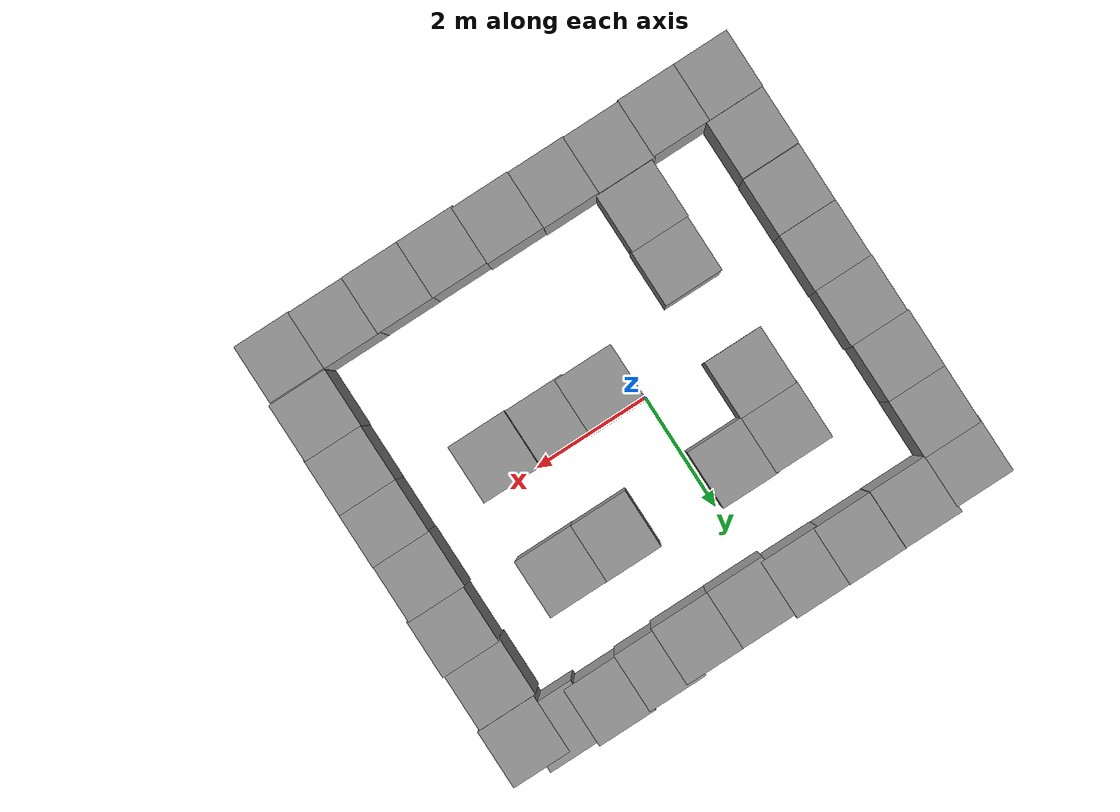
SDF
<?xml version='1.0'?>
<sdf version='1.7'>
  <model name='turtlebot3_world'>
    <link name='link_4'>
      <inertial>
        <mass>1</mass>
        <inertia>
          <ixx>0.166667</ixx>
          <ixy>0</ixy>
          <ixz>0</ixz>
          <iyy>0.166667</iyy>
          <iyz>0</iyz>
          <izz>0.166667</izz>
        </inertia>
      </inertial>
      <pose>-3.51588 2.52725 0.5 0 -0 0</pose>
      <visual name='visual'>
        <pose>0 0 0 0 -0 0</pose>
        <geometry>
          <box>
            <size>1 1 1</size>
          </box>
        </geometry>
        <material>
          <lighting>1</lighting>
          <script>
            <uri>file://media/materials/scripts/gazebo.material</uri>
            <name>Gazebo/Grey</name>
          </script>
          <shader type='pixel'/>
        </material>
        <transparency>0</transparency>
        <cast_shadows>1</cast_shadows>
      </visual>
      <collision name='collision'>
        <laser_retro>0</laser_retro>
        <max_contacts>10</max_contacts>
        <pose>0 0 0 0 -0 0</pose>
        <geometry>
          <box>
            <size>1 1 1</size>
          </box>
        </geometry>
        <surface>
          <friction>
            <ode>
              <mu>1</mu>
              <mu2>1</mu2>
              <fdir1>0 0 0</fdir1>
              <slip1>0</slip1>
              <slip2>0</slip2>
            </ode>
            <torsional>
              <coefficient>1</coefficient>
              <patch_radius>0</patch_radius>
              <surface_radius>0</surface_radius>
              <use_patch_radius>1</use_patch_radius>
              <ode>
                <slip>0</slip>
              </ode>
            </torsional>
          </friction>
          <bounce>
            <restitution_coefficient>0</restitution_coefficient>
            <threshold>1e+06</threshold>
          </bounce>
          <contact>
            <collide_without_contact>0</collide_without_contact>
            <collide_without_contact_bitmask>1</collide_without_contact_bitmask>
            <collide_bitmask>1</collide_bitmask>
            <ode>
              <soft_cfm>0</soft_cfm>
              <soft_erp>0.2</soft_erp>
              <kp>1e+13</kp>
              <kd>1</kd>
              <max_vel>0.01</max_vel>
              <min_depth>0</min_depth>
            </ode>
            <bullet>
              <split_impulse>1</split_impulse>
              <split_impulse_penetration_threshold>-0.01</split_impulse_penetration_threshold>
              <soft_cfm>0</soft_cfm>
              <soft_erp>0.2</soft_erp>
              <kp>1e+13</kp>
              <kd>1</kd>
            </bullet>
          </contact>
        </surface>
      </collision>
    </link>
    <link name='link_4_clone'>
      <inertial>
        <mass>1</mass>
        <inertia>
          <ixx>0.166667</ixx>
          <ixy>0</ixy>
          <ixz>0</ixz>
          <iyy>0.166667</iyy>
          <iyz>0</iyz>
          <izz>0.166667</izz>
        </inertia>
      </inertial>
      <pose>-3.51881 1.52869 0.5 0 -0 0</pose>
      <visual name='visual'>
        <pose>0 0 0 0 -0 0</pose>
        <geometry>
          <box>
            <size>1 1 1</size>
          </box>
        </geometry>
        <material>
          <lighting>1</lighting>
          <script>
            <uri>file://media/materials/scripts/gazebo.material</uri>
            <name>Gazebo/Grey</name>
          </script>
          <shader type='pixel'/>
        </material>
        <transparency>0</transparency>
        <cast_shadows>1</cast_shadows>
      </visual>
      <collision name='collision'>
        <laser_retro>0</laser_retro>
        <max_contacts>10</max_contacts>
        <pose>0 0 0 0 -0 0</pose>
        <geometry>
          <box>
            <size>1 1 1</size>
          </box>
        </geometry>
        <surface>
          <friction>
            <ode>
              <mu>1</mu>
              <mu2>1</mu2>
              <fdir1>0 0 0</fdir1>
              <slip1>0</slip1>
              <slip2>0</slip2>
            </ode>
            <torsional>
              <coefficient>1</coefficient>
              <patch_radius>0</patch_radius>
              <surface_radius>0</surface_radius>
              <use_patch_radius>1</use_patch_radius>
              <ode>
                <slip>0</slip>
              </ode>
            </torsional>
          </friction>
          <bounce>
            <restitution_coefficient>0</restitution_coefficient>
            <threshold>1e+06</threshold>
          </bounce>
          <contact>
            <collide_without_contact>0</collide_without_contact>
            <collide_without_contact_bitmask>1</collide_without_contact_bitmask>
            <collide_bitmask>1</collide_bitmask>
            <ode>
              <soft_cfm>0</soft_cfm>
              <soft_erp>0.2</soft_erp>
              <kp>1e+13</kp>
              <kd>1</kd>
              <max_vel>0.01</max_vel>
              <min_depth>0</min_depth>
            </ode>
            <bullet>
              <split_impulse>1</split_impulse>
              <split_impulse_penetration_threshold>-0.01</split_impulse_penetration_threshold>
              <soft_cfm>0</soft_cfm>
              <soft_erp>0.2</soft_erp>
              <kp>1e+13</kp>
              <kd>1</kd>
            </bullet>
          </contact>
        </surface>
      </collision>
    </link>
    <link name='link_4_clone_0'>
      <inertial>
        <mass>1</mass>
        <inertia>
          <ixx>0.166667</ixx>
          <ixy>0</ixy>
          <ixz>0</ixz>
          <iyy>0.166667</iyy>
          <iyz>0</iyz>
          <izz>0.166667</izz>
        </inertia>
      </inertial>
      <pose>-3.49974 0.540999 0.5 0 -0 0</pose>
      <visual name='visual'>
        <pose>0 0 0 0 -0 0</pose>
        <geometry>
          <box>
            <size>1 1 1</size>
          </box>
        </geometry>
        <material>
          <lighting>1</lighting>
          <script>
            <uri>file://media/materials/scripts/gazebo.material</uri>
            <name>Gazebo/Grey</name>
          </script>
          <shader type='pixel'/>
        </material>
        <transparency>0</transparency>
        <cast_shadows>1</cast_shadows>
      </visual>
      <collision name='collision'>
        <laser_retro>0</laser_retro>
        <max_contacts>10</max_contacts>
        <pose>0 0 0 0 -0 0</pose>
        <geometry>
          <box>
            <size>1 1 1</size>
          </box>
        </geometry>
        <surface>
          <friction>
            <ode>
              <mu>1</mu>
              <mu2>1</mu2>
              <fdir1>0 0 0</fdir1>
              <slip1>0</slip1>
              <slip2>0</slip2>
            </ode>
            <torsional>
              <coefficient>1</coefficient>
              <patch_radius>0</patch_radius>
              <surface_radius>0</surface_radius>
              <use_patch_radius>1</use_patch_radius>
              <ode>
                <slip>0</slip>
              </ode>
            </torsional>
          </friction>
          <bounce>
            <restitution_coefficient>0</restitution_coefficient>
            <threshold>1e+06</threshold>
          </bounce>
          <contact>
            <collide_without_contact>0</collide_without_contact>
            <collide_without_contact_bitmask>1</collide_without_contact_bitmask>
            <collide_bitmask>1</collide_bitmask>
            <ode>
              <soft_cfm>0</soft_cfm>
              <soft_erp>0.2</soft_erp>
              <kp>1e+13</kp>
              <kd>1</kd>
              <max_vel>0.01</max_vel>
              <min_depth>0</min_depth>
            </ode>
            <bullet>
              <split_impulse>1</split_impulse>
              <split_impulse_penetration_threshold>-0.01</split_impulse_penetration_threshold>
              <soft_cfm>0</soft_cfm>
              <soft_erp>0.2</soft_erp>
              <kp>1e+13</kp>
              <kd>1</kd>
            </bullet>
          </contact>
        </surface>
      </collision>
    </link>
    <link name='link_4_clone_1'>
      <inertial>
        <mass>1</mass>
        <inertia>
          <ixx>0.166667</ixx>
          <ixy>0</ixy>
          <ixz>0</ixz>
          <iyy>0.166667</iyy>
          <iyz>0</iyz>
          <izz>0.166667</izz>
        </inertia>
      </inertial>
      <pose>-3.49177 -0.443894 0.5 0 -0 0</pose>
      <visual name='visual'>
        <pose>0 0 0 0 -0 0</pose>
        <geometry>
          <box>
            <size>1 1 1</size>
          </box>
        </geometry>
        <material>
          <lighting>1</lighting>
          <script>
            <uri>file://media/materials/scripts/gazebo.material</uri>
            <name>Gazebo/Grey</name>
          </script>
          <shader type='pixel'/>
        </material>
        <transparency>0</transparency>
        <cast_shadows>1</cast_shadows>
      </visual>
      <collision name='collision'>
        <laser_retro>0</laser_retro>
        <max_contacts>10</max_contacts>
        <pose>0 0 0 0 -0 0</pose>
        <geometry>
          <box>
            <size>1 1 1</size>
          </box>
        </geometry>
        <surface>
          <friction>
            <ode>
              <mu>1</mu>
              <mu2>1</mu2>
              <fdir1>0 0 0</fdir1>
              <slip1>0</slip1>
              <slip2>0</slip2>
            </ode>
            <torsional>
              <coefficient>1</coefficient>
              <patch_radius>0</patch_radius>
              <surface_radius>0</surface_radius>
              <use_patch_radius>1</use_patch_radius>
              <ode>
                <slip>0</slip>
              </ode>
            </torsional>
          </friction>
          <bounce>
            <restitution_coefficient>0</restitution_coefficient>
            <threshold>1e+06</threshold>
          </bounce>
          <contact>
            <collide_without_contact>0</collide_without_contact>
            <collide_without_contact_bitmask>1</collide_without_contact_bitmask>
            <collide_bitmask>1</collide_bitmask>
            <ode>
              <soft_cfm>0</soft_cfm>
              <soft_erp>0.2</soft_erp>
              <kp>1e+13</kp>
              <kd>1</kd>
              <max_vel>0.01</max_vel>
              <min_depth>0</min_depth>
            </ode>
            <bullet>
              <split_impulse>1</split_impulse>
              <split_impulse_penetration_threshold>-0.01</split_impulse_penetration_threshold>
              <soft_cfm>0</soft_cfm>
              <soft_erp>0.2</soft_erp>
              <kp>1e+13</kp>
              <kd>1</kd>
            </bullet>
          </contact>
        </surface>
      </collision>
    </link>
    <link name='link_4_clone_10'>
      <inertial>
        <mass>1</mass>
        <inertia>
          <ixx>0.166667</ixx>
          <ixy>0</ixy>
          <ixz>0</ixz>
          <iyy>0.166667</iyy>
          <iyz>0</iyz>
          <izz>0.166667</izz>
        </inertia>
      </inertial>
      <pose>1.31695 3.4392 0.5 0 -0 0</pose>
      <visual name='visual'>
        <pose>0 0 0 0 -0 0</pose>
        <geometry>
          <box>
            <size>1 1 1</size>
          </box>
        </geometry>
        <material>
          <lighting>1</lighting>
          <script>
            <uri>file://media/materials/scripts/gazebo.material</uri>
            <name>Gazebo/Grey</name>
          </script>
          <shader type='pixel'/>
        </material>
        <transparency>0</transparency>
        <cast_shadows>1</cast_shadows>
      </visual>
      <collision name='collision'>
        <laser_retro>0</laser_retro>
        <max_contacts>10</max_contacts>
        <pose>0 0 0 0 -0 0</pose>
        <geometry>
          <box>
            <size>1 1 1</size>
          </box>
        </geometry>
        <surface>
          <friction>
            <ode>
              <mu>1</mu>
              <mu2>1</mu2>
              <fdir1>0 0 0</fdir1>
              <slip1>0</slip1>
              <slip2>0</slip2>
            </ode>
            <torsional>
              <coefficient>1</coefficient>
              <patch_radius>0</patch_radius>
              <surface_radius>0</surface_radius>
              <use_patch_radius>1</use_patch_radius>
              <ode>
                <slip>0</slip>
              </ode>
            </torsional>
          </friction>
          <bounce>
            <restitution_coefficient>0</restitution_coefficient>
            <threshold>1e+06</threshold>
          </bounce>
          <contact>
            <collide_without_contact>0</collide_without_contact>
            <collide_without_contact_bitmask>1</collide_without_contact_bitmask>
            <collide_bitmask>1</collide_bitmask>
            <ode>
              <soft_cfm>0</soft_cfm>
              <soft_erp>0.2</soft_erp>
              <kp>1e+13</kp>
              <kd>1</kd>
              <max_vel>0.01</max_vel>
              <min_depth>0</min_depth>
            </ode>
            <bullet>
              <split_impulse>1</split_impulse>
              <split_impulse_penetration_threshold>-0.01</split_impulse_penetration_threshold>
              <soft_cfm>0</soft_cfm>
              <soft_erp>0.2</soft_erp>
              <kp>1e+13</kp>
              <kd>1</kd>
            </bullet>
          </contact>
        </surface>
      </collision>
    </link>
    <link name='link_4_clone_11'>
      <inertial>
        <mass>1</mass>
        <inertia>
          <ixx>0.166667</ixx>
          <ixy>0</ixy>
          <ixz>0</ixz>
          <iyy>0.166667</iyy>
          <iyz>0</iyz>
          <izz>0.166667</izz>
        </inertia>
      </inertial>
      <pose>2.00157 3.47266 0.5 0 -0 0</pose>
      <visual name='visual'>
        <pose>0 0 0 0 -0 0</pose>
        <geometry>
          <box>
            <size>1 1 1</size>
          </box>
        </geometry>
        <material>
          <lighting>1</lighting>
          <script>
            <uri>file://media/materials/scripts/gazebo.material</uri>
            <name>Gazebo/Grey</name>
          </script>
          <shader type='pixel'/>
        </material>
        <transparency>0</transparency>
        <cast_shadows>1</cast_shadows>
      </visual>
      <collision name='collision'>
        <laser_retro>0</laser_retro>
        <max_contacts>10</max_contacts>
        <pose>0 0 0 0 -0 0</pose>
        <geometry>
          <box>
            <size>1 1 1</size>
          </box>
        </geometry>
        <surface>
          <friction>
            <ode>
              <mu>1</mu>
              <mu2>1</mu2>
              <fdir1>0 0 0</fdir1>
              <slip1>0</slip1>
              <slip2>0</slip2>
            </ode>
            <torsional>
              <coefficient>1</coefficient>
              <patch_radius>0</patch_radius>
              <surface_radius>0</surface_radius>
              <use_patch_radius>1</use_patch_radius>
              <ode>
                <slip>0</slip>
              </ode>
            </torsional>
          </friction>
          <bounce>
            <restitution_coefficient>0</restitution_coefficient>
            <threshold>1e+06</threshold>
          </bounce>
          <contact>
            <collide_without_contact>0</collide_without_contact>
            <collide_without_contact_bitmask>1</collide_without_contact_bitmask>
            <collide_bitmask>1</collide_bitmask>
            <ode>
              <soft_cfm>0</soft_cfm>
              <soft_erp>0.2</soft_erp>
              <kp>1e+13</kp>
              <kd>1</kd>
              <max_vel>0.01</max_vel>
              <min_depth>0</min_depth>
            </ode>
            <bullet>
              <split_impulse>1</split_impulse>
              <split_impulse_penetration_threshold>-0.01</split_impulse_penetration_threshold>
              <soft_cfm>0</soft_cfm>
              <soft_erp>0.2</soft_erp>
              <kp>1e+13</kp>
              <kd>1</kd>
            </bullet>
          </contact>
        </surface>
      </collision>
    </link>
    <link name='link_4_clone_12'>
      <inertial>
        <mass>1</mass>
        <inertia>
          <ixx>0.166667</ixx>
          <ixy>0</ixy>
          <ixz>0</ixz>
          <iyy>0.166667</iyy>
          <iyz>0</iyz>
          <izz>0.166667</izz>
        </inertia>
      </inertial>
      <pose>2.91323 3.4956 0.5 0 -0 0</pose>
      <visual name='visual'>
        <pose>0 0 0 0 -0 0</pose>
        <geometry>
          <box>
            <size>1 1 1</size>
          </box>
        </geometry>
        <material>
          <lighting>1</lighting>
          <script>
            <uri>file://media/materials/scripts/gazebo.material</uri>
            <name>Gazebo/Grey</name>
          </script>
          <shader type='pixel'/>
        </material>
        <transparency>0</transparency>
        <cast_shadows>1</cast_shadows>
      </visual>
      <collision name='collision'>
        <laser_retro>0</laser_retro>
        <max_contacts>10</max_contacts>
        <pose>0 0 0 0 -0 0</pose>
        <geometry>
          <box>
            <size>1 1 1</size>
          </box>
        </geometry>
        <surface>
          <friction>
            <ode>
              <mu>1</mu>
              <mu2>1</mu2>
              <fdir1>0 0 0</fdir1>
              <slip1>0</slip1>
              <slip2>0</slip2>
            </ode>
            <torsional>
              <coefficient>1</coefficient>
              <patch_radius>0</patch_radius>
              <surface_radius>0</surface_radius>
              <use_patch_radius>1</use_patch_radius>
              <ode>
                <slip>0</slip>
              </ode>
            </torsional>
          </friction>
          <bounce>
            <restitution_coefficient>0</restitution_coefficient>
            <threshold>1e+06</threshold>
          </bounce>
          <contact>
            <collide_without_contact>0</collide_without_contact>
            <collide_without_contact_bitmask>1</collide_without_contact_bitmask>
            <collide_bitmask>1</collide_bitmask>
            <ode>
              <soft_cfm>0</soft_cfm>
              <soft_erp>0.2</soft_erp>
              <kp>1e+13</kp>
              <kd>1</kd>
              <max_vel>0.01</max_vel>
              <min_depth>0</min_depth>
            </ode>
            <bullet>
              <split_impulse>1</split_impulse>
              <split_impulse_penetration_threshold>-0.01</split_impulse_penetration_threshold>
              <soft_cfm>0</soft_cfm>
              <soft_erp>0.2</soft_erp>
              <kp>1e+13</kp>
              <kd>1</kd>
            </bullet>
          </contact>
        </surface>
      </collision>
    </link>
    <link name='link_4_clone_13'>
      <inertial>
        <mass>1</mass>
        <inertia>
          <ixx>0.166667</ixx>
          <ixy>0</ixy>
          <ixz>0</ixz>
          <iyy>0.166667</iyy>
          <iyz>0</iyz>
          <izz>0.166667</izz>
        </inertia>
      </inertial>
      <pose>-2.56143 -3.46208 0.5 0 -0 0</pose>
      <visual name='visual'>
        <pose>0 0 0 0 -0 0</pose>
        <geometry>
          <box>
            <size>1 1 1</size>
          </box>
        </geometry>
        <material>
          <lighting>1</lighting>
          <script>
            <uri>file://media/materials/scripts/gazebo.material</uri>
            <name>Gazebo/Grey</name>
          </script>
          <shader type='pixel'/>
        </material>
        <transparency>0</transparency>
        <cast_shadows>1</cast_shadows>
      </visual>
      <collision name='collision'>
        <laser_retro>0</laser_retro>
        <max_contacts>10</max_contacts>
        <pose>0 0 0 0 -0 0</pose>
        <geometry>
          <box>
            <size>1 1 1</size>
          </box>
        </geometry>
        <surface>
          <friction>
            <ode>
              <mu>1</mu>
              <mu2>1</mu2>
              <fdir1>0 0 0</fdir1>
              <slip1>0</slip1>
              <slip2>0</slip2>
            </ode>
            <torsional>
              <coefficient>1</coefficient>
              <patch_radius>0</patch_radius>
              <surface_radius>0</surface_radius>
              <use_patch_radius>1</use_patch_radius>
              <ode>
                <slip>0</slip>
              </ode>
            </torsional>
          </friction>
          <bounce>
            <restitution_coefficient>0</restitution_coefficient>
            <threshold>1e+06</threshold>
          </bounce>
          <contact>
            <collide_without_contact>0</collide_without_contact>
            <collide_without_contact_bitmask>1</collide_without_contact_bitmask>
            <collide_bitmask>1</collide_bitmask>
            <ode>
              <soft_cfm>0</soft_cfm>
              <soft_erp>0.2</soft_erp>
              <kp>1e+13</kp>
              <kd>1</kd>
              <max_vel>0.01</max_vel>
              <min_depth>0</min_depth>
            </ode>
            <bullet>
              <split_impulse>1</split_impulse>
              <split_impulse_penetration_threshold>-0.01</split_impulse_penetration_threshold>
              <soft_cfm>0</soft_cfm>
              <soft_erp>0.2</soft_erp>
              <kp>1e+13</kp>
              <kd>1</kd>
            </bullet>
          </contact>
        </surface>
      </collision>
    </link>
    <link name='link_4_clone_14'>
      <inertial>
        <mass>1</mass>
        <inertia>
          <ixx>0.166667</ixx>
          <ixy>0</ixy>
          <ixz>0</ixz>
          <iyy>0.166667</iyy>
          <iyz>0</iyz>
          <izz>0.166667</izz>
        </inertia>
      </inertial>
      <pose>-1.57857 -3.44426 0.5 0 -0 0</pose>
      <visual name='visual'>
        <pose>0 0 0 0 -0 0</pose>
        <geometry>
          <box>
            <size>1 1 1</size>
          </box>
        </geometry>
        <material>
          <lighting>1</lighting>
          <script>
            <uri>file://media/materials/scripts/gazebo.material</uri>
            <name>Gazebo/Grey</name>
          </script>
          <shader type='pixel'/>
        </material>
        <transparency>0</transparency>
        <cast_shadows>1</cast_shadows>
      </visual>
      <collision name='collision'>
        <laser_retro>0</laser_retro>
        <max_contacts>10</max_contacts>
        <pose>0 0 0 0 -0 0</pose>
        <geometry>
          <box>
            <size>1 1 1</size>
          </box>
        </geometry>
        <surface>
          <friction>
            <ode>
              <mu>1</mu>
              <mu2>1</mu2>
              <fdir1>0 0 0</fdir1>
              <slip1>0</slip1>
              <slip2>0</slip2>
            </ode>
            <torsional>
              <coefficient>1</coefficient>
              <patch_radius>0</patch_radius>
              <surface_radius>0</surface_radius>
              <use_patch_radius>1</use_patch_radius>
              <ode>
                <slip>0</slip>
              </ode>
            </torsional>
          </friction>
          <bounce>
            <restitution_coefficient>0</restitution_coefficient>
            <threshold>1e+06</threshold>
          </bounce>
          <contact>
            <collide_without_contact>0</collide_without_contact>
            <collide_without_contact_bitmask>1</collide_without_contact_bitmask>
            <collide_bitmask>1</collide_bitmask>
            <ode>
              <soft_cfm>0</soft_cfm>
              <soft_erp>0.2</soft_erp>
              <kp>1e+13</kp>
              <kd>1</kd>
              <max_vel>0.01</max_vel>
              <min_depth>0</min_depth>
            </ode>
            <bullet>
              <split_impulse>1</split_impulse>
              <split_impulse_penetration_threshold>-0.01</split_impulse_penetration_threshold>
              <soft_cfm>0</soft_cfm>
              <soft_erp>0.2</soft_erp>
              <kp>1e+13</kp>
              <kd>1</kd>
            </bullet>
          </contact>
        </surface>
      </collision>
    </link>
    <link name='link_4_clone_15'>
      <inertial>
        <mass>1</mass>
        <inertia>
          <ixx>0.166667</ixx>
          <ixy>0</ixy>
          <ixz>0</ixz>
          <iyy>0.166667</iyy>
          <iyz>0</iyz>
          <izz>0.166667</izz>
        </inertia>
      </inertial>
      <pose>-0.599535 -3.45421 0.5 0 -0 0</pose>
      <visual name='visual'>
        <pose>0 0 0 0 -0 0</pose>
        <geometry>
          <box>
            <size>1 1 1</size>
          </box>
        </geometry>
        <material>
          <lighting>1</lighting>
          <script>
            <uri>file://media/materials/scripts/gazebo.material</uri>
            <name>Gazebo/Grey</name>
          </script>
          <shader type='pixel'/>
        </material>
        <transparency>0</transparency>
        <cast_shadows>1</cast_shadows>
      </visual>
      <collision name='collision'>
        <laser_retro>0</laser_retro>
        <max_contacts>10</max_contacts>
        <pose>0 0 0 0 -0 0</pose>
        <geometry>
          <box>
            <size>1 1 1</size>
          </box>
        </geometry>
        <surface>
          <friction>
            <ode>
              <mu>1</mu>
              <mu2>1</mu2>
              <fdir1>0 0 0</fdir1>
              <slip1>0</slip1>
              <slip2>0</slip2>
            </ode>
            <torsional>
              <coefficient>1</coefficient>
              <patch_radius>0</patch_radius>
              <surface_radius>0</surface_radius>
              <use_patch_radius>1</use_patch_radius>
              <ode>
                <slip>0</slip>
              </ode>
            </torsional>
          </friction>
          <bounce>
            <restitution_coefficient>0</restitution_coefficient>
            <threshold>1e+06</threshold>
          </bounce>
          <contact>
            <collide_without_contact>0</collide_without_contact>
            <collide_without_contact_bitmask>1</collide_without_contact_bitmask>
            <collide_bitmask>1</collide_bitmask>
            <ode>
              <soft_cfm>0</soft_cfm>
              <soft_erp>0.2</soft_erp>
              <kp>1e+13</kp>
              <kd>1</kd>
              <max_vel>0.01</max_vel>
              <min_depth>0</min_depth>
            </ode>
            <bullet>
              <split_impulse>1</split_impulse>
              <split_impulse_penetration_threshold>-0.01</split_impulse_penetration_threshold>
              <soft_cfm>0</soft_cfm>
              <soft_erp>0.2</soft_erp>
              <kp>1e+13</kp>
              <kd>1</kd>
            </bullet>
          </contact>
        </surface>
      </collision>
    </link>
    <link name='link_4_clone_16'>
      <inertial>
        <mass>1</mass>
        <inertia>
          <ixx>0.166667</ixx>
          <ixy>0</ixy>
          <ixz>0</ixz>
          <iyy>0.166667</iyy>
          <iyz>0</iyz>
          <izz>0.166667</izz>
        </inertia>
      </inertial>
      <pose>0.398656 -3.46623 0.5 0 -0 0</pose>
      <visual name='visual'>
        <pose>0 0 0 0 -0 0</pose>
        <geometry>
          <box>
            <size>1 1 1</size>
          </box>
        </geometry>
        <material>
          <lighting>1</lighting>
          <script>
            <uri>file://media/materials/scripts/gazebo.material</uri>
            <name>Gazebo/Grey</name>
          </script>
          <shader type='pixel'/>
        </material>
        <transparency>0</transparency>
        <cast_shadows>1</cast_shadows>
      </visual>
      <collision name='collision'>
        <laser_retro>0</laser_retro>
        <max_contacts>10</max_contacts>
        <pose>0 0 0 0 -0 0</pose>
        <geometry>
          <box>
            <size>1 1 1</size>
          </box>
        </geometry>
        <surface>
          <friction>
            <ode>
              <mu>1</mu>
              <mu2>1</mu2>
              <fdir1>0 0 0</fdir1>
              <slip1>0</slip1>
              <slip2>0</slip2>
            </ode>
            <torsional>
              <coefficient>1</coefficient>
              <patch_radius>0</patch_radius>
              <surface_radius>0</surface_radius>
              <use_patch_radius>1</use_patch_radius>
              <ode>
                <slip>0</slip>
              </ode>
            </torsional>
          </friction>
          <bounce>
            <restitution_coefficient>0</restitution_coefficient>
            <threshold>1e+06</threshold>
          </bounce>
          <contact>
            <collide_without_contact>0</collide_without_contact>
            <collide_without_contact_bitmask>1</collide_without_contact_bitmask>
            <collide_bitmask>1</collide_bitmask>
            <ode>
              <soft_cfm>0</soft_cfm>
              <soft_erp>0.2</soft_erp>
              <kp>1e+13</kp>
              <kd>1</kd>
              <max_vel>0.01</max_vel>
              <min_depth>0</min_depth>
            </ode>
            <bullet>
              <split_impulse>1</split_impulse>
              <split_impulse_penetration_threshold>-0.01</split_impulse_penetration_threshold>
              <soft_cfm>0</soft_cfm>
              <soft_erp>0.2</soft_erp>
              <kp>1e+13</kp>
              <kd>1</kd>
            </bullet>
          </contact>
        </surface>
      </collision>
    </link>
    <link name='link_4_clone_17'>
      <inertial>
        <mass>1</mass>
        <inertia>
          <ixx>0.166667</ixx>
          <ixy>0</ixy>
          <ixz>0</ixz>
          <iyy>0.166667</iyy>
          <iyz>0</iyz>
          <izz>0.166667</izz>
        </inertia>
      </inertial>
      <pose>1.36667 -3.48701 0.5 0 -0 0</pose>
      <visual name='visual'>
        <pose>0 0 0 0 -0 0</pose>
        <geometry>
          <box>
            <size>1 1 1</size>
          </box>
        </geometry>
        <material>
          <lighting>1</lighting>
          <script>
            <uri>file://media/materials/scripts/gazebo.material</uri>
            <name>Gazebo/Grey</name>
          </script>
          <shader type='pixel'/>
        </material>
        <transparency>0</transparency>
        <cast_shadows>1</cast_shadows>
      </visual>
      <collision name='collision'>
        <laser_retro>0</laser_retro>
        <max_contacts>10</max_contacts>
        <pose>0 0 0 0 -0 0</pose>
        <geometry>
          <box>
            <size>1 1 1</size>
          </box>
        </geometry>
        <surface>
          <friction>
            <ode>
              <mu>1</mu>
              <mu2>1</mu2>
              <fdir1>0 0 0</fdir1>
              <slip1>0</slip1>
              <slip2>0</slip2>
            </ode>
            <torsional>
              <coefficient>1</coefficient>
              <patch_radius>0</patch_radius>
              <surface_radius>0</surface_radius>
              <use_patch_radius>1</use_patch_radius>
              <ode>
                <slip>0</slip>
              </ode>
            </torsional>
          </friction>
          <bounce>
            <restitution_coefficient>0</restitution_coefficient>
            <threshold>1e+06</threshold>
          </bounce>
          <contact>
            <collide_without_contact>0</collide_without_contact>
            <collide_without_contact_bitmask>1</collide_without_contact_bitmask>
            <collide_bitmask>1</collide_bitmask>
            <ode>
              <soft_cfm>0</soft_cfm>
              <soft_erp>0.2</soft_erp>
              <kp>1e+13</kp>
              <kd>1</kd>
              <max_vel>0.01</max_vel>
              <min_depth>0</min_depth>
            </ode>
            <bullet>
              <split_impulse>1</split_impulse>
              <split_impulse_penetration_threshold>-0.01</split_impulse_penetration_threshold>
              <soft_cfm>0</soft_cfm>
              <soft_erp>0.2</soft_erp>
              <kp>1e+13</kp>
              <kd>1</kd>
            </bullet>
          </contact>
        </surface>
      </collision>
    </link>
    <link name='link_4_clone_18'>
      <inertial>
        <mass>1</mass>
        <inertia>
          <ixx>0.166667</ixx>
          <ixy>0</ixy>
          <ixz>0</ixz>
          <iyy>0.166667</iyy>
          <iyz>0</iyz>
          <izz>0.166667</izz>
        </inertia>
      </inertial>
      <pose>2.34696 -3.48647 0.5 0 -0 0</pose>
      <visual name='visual'>
        <pose>0 0 0 0 -0 0</pose>
        <geometry>
          <box>
            <size>1 1 1</size>
          </box>
        </geometry>
        <material>
          <lighting>1</lighting>
          <script>
            <uri>file://media/materials/scripts/gazebo.material</uri>
            <name>Gazebo/Grey</name>
          </script>
          <shader type='pixel'/>
        </material>
        <transparency>0</transparency>
        <cast_shadows>1</cast_shadows>
      </visual>
      <collision name='collision'>
        <laser_retro>0</laser_retro>
        <max_contacts>10</max_contacts>
        <pose>0 0 0 0 -0 0</pose>
        <geometry>
          <box>
            <size>1 1 1</size>
          </box>
        </geometry>
        <surface>
          <friction>
            <ode>
              <mu>1</mu>
              <mu2>1</mu2>
              <fdir1>0 0 0</fdir1>
              <slip1>0</slip1>
              <slip2>0</slip2>
            </ode>
            <torsional>
              <coefficient>1</coefficient>
              <patch_radius>0</patch_radius>
              <surface_radius>0</surface_radius>
              <use_patch_radius>1</use_patch_radius>
              <ode>
                <slip>0</slip>
              </ode>
            </torsional>
          </friction>
          <bounce>
            <restitution_coefficient>0</restitution_coefficient>
            <threshold>1e+06</threshold>
          </bounce>
          <contact>
            <collide_without_contact>0</collide_without_contact>
            <collide_without_contact_bitmask>1</collide_without_contact_bitmask>
            <collide_bitmask>1</collide_bitmask>
            <ode>
              <soft_cfm>0</soft_cfm>
              <soft_erp>0.2</soft_erp>
              <kp>1e+13</kp>
              <kd>1</kd>
              <max_vel>0.01</max_vel>
              <min_depth>0</min_depth>
            </ode>
            <bullet>
              <split_impulse>1</split_impulse>
              <split_impulse_penetration_threshold>-0.01</split_impulse_penetration_threshold>
              <soft_cfm>0</soft_cfm>
              <soft_erp>0.2</soft_erp>
              <kp>1e+13</kp>
              <kd>1</kd>
            </bullet>
          </contact>
        </surface>
      </collision>
    </link>
    <link name='link_4_clone_19'>
      <inertial>
        <mass>1</mass>
        <inertia>
          <ixx>0.166667</ixx>
          <ixy>0</ixy>
          <ixz>0</ixz>
          <iyy>0.166667</iyy>
          <iyz>0</iyz>
          <izz>0.166667</izz>
        </inertia>
      </inertial>
      <pose>3.30228 -3.48091 0.5 0 -0 0</pose>
      <visual name='visual'>
        <pose>0 0 0 0 -0 0</pose>
        <geometry>
          <box>
            <size>1 1 1</size>
          </box>
        </geometry>
        <material>
          <lighting>1</lighting>
          <script>
            <uri>file://media/materials/scripts/gazebo.material</uri>
            <name>Gazebo/Grey</name>
          </script>
          <shader type='pixel'/>
        </material>
        <transparency>0</transparency>
        <cast_shadows>1</cast_shadows>
      </visual>
      <collision name='collision'>
        <laser_retro>0</laser_retro>
        <max_contacts>10</max_contacts>
        <pose>0 0 0 0 -0 0</pose>
        <geometry>
          <box>
            <size>1 1 1</size>
          </box>
        </geometry>
        <surface>
          <friction>
            <ode>
              <mu>1</mu>
              <mu2>1</mu2>
              <fdir1>0 0 0</fdir1>
              <slip1>0</slip1>
              <slip2>0</slip2>
            </ode>
            <torsional>
              <coefficient>1</coefficient>
              <patch_radius>0</patch_radius>
              <surface_radius>0</surface_radius>
              <use_patch_radius>1</use_patch_radius>
              <ode>
                <slip>0</slip>
              </ode>
            </torsional>
          </friction>
          <bounce>
            <restitution_coefficient>0</restitution_coefficient>
            <threshold>1e+06</threshold>
          </bounce>
          <contact>
            <collide_without_contact>0</collide_without_contact>
            <collide_without_contact_bitmask>1</collide_without_contact_bitmask>
            <collide_bitmask>1</collide_bitmask>
            <ode>
              <soft_cfm>0</soft_cfm>
              <soft_erp>0.2</soft_erp>
              <kp>1e+13</kp>
              <kd>1</kd>
              <max_vel>0.01</max_vel>
              <min_depth>0</min_depth>
            </ode>
            <bullet>
              <split_impulse>1</split_impulse>
              <split_impulse_penetration_threshold>-0.01</split_impulse_penetration_threshold>
              <soft_cfm>0</soft_cfm>
              <soft_erp>0.2</soft_erp>
              <kp>1e+13</kp>
              <kd>1</kd>
            </bullet>
          </contact>
        </surface>
      </collision>
    </link>
    <link name='link_4_clone_2'>
      <inertial>
        <mass>1</mass>
        <inertia>
          <ixx>0.166667</ixx>
          <ixy>0</ixy>
          <ixz>0</ixz>
          <iyy>0.166667</iyy>
          <iyz>0</iyz>
          <izz>0.166667</izz>
        </inertia>
      </inertial>
      <pose>-3.49078 -1.44711 0.5 0 -0 0</pose>
      <visual name='visual'>
        <pose>0 0 0 0 -0 0</pose>
        <geometry>
          <box>
            <size>1 1 1</size>
          </box>
        </geometry>
        <material>
          <lighting>1</lighting>
          <script>
            <uri>file://media/materials/scripts/gazebo.material</uri>
            <name>Gazebo/Grey</name>
          </script>
          <shader type='pixel'/>
        </material>
        <transparency>0</transparency>
        <cast_shadows>1</cast_shadows>
      </visual>
      <collision name='collision'>
        <laser_retro>0</laser_retro>
        <max_contacts>10</max_contacts>
        <pose>0 0 0 0 -0 0</pose>
        <geometry>
          <box>
            <size>1 1 1</size>
          </box>
        </geometry>
        <surface>
          <friction>
            <ode>
              <mu>1</mu>
              <mu2>1</mu2>
              <fdir1>0 0 0</fdir1>
              <slip1>0</slip1>
              <slip2>0</slip2>
            </ode>
            <torsional>
              <coefficient>1</coefficient>
              <patch_radius>0</patch_radius>
              <surface_radius>0</surface_radius>
              <use_patch_radius>1</use_patch_radius>
              <ode>
                <slip>0</slip>
              </ode>
            </torsional>
          </friction>
          <bounce>
            <restitution_coefficient>0</restitution_coefficient>
            <threshold>1e+06</threshold>
          </bounce>
          <contact>
            <collide_without_contact>0</collide_without_contact>
            <collide_without_contact_bitmask>1</collide_without_contact_bitmask>
            <collide_bitmask>1</collide_bitmask>
            <ode>
              <soft_cfm>0</soft_cfm>
              <soft_erp>0.2</soft_erp>
              <kp>1e+13</kp>
              <kd>1</kd>
              <max_vel>0.01</max_vel>
              <min_depth>0</min_depth>
            </ode>
            <bullet>
              <split_impulse>1</split_impulse>
              <split_impulse_penetration_threshold>-0.01</split_impulse_penetration_threshold>
              <soft_cfm>0</soft_cfm>
              <soft_erp>0.2</soft_erp>
              <kp>1e+13</kp>
              <kd>1</kd>
            </bullet>
          </contact>
        </surface>
      </collision>
    </link>
    <link name='link_4_clone_20'>
      <inertial>
        <mass>1</mass>
        <inertia>
          <ixx>0.166667</ixx>
          <ixy>0</ixy>
          <ixz>0</ixz>
          <iyy>0.166667</iyy>
          <iyz>0</iyz>
          <izz>0.166667</izz>
        </inertia>
      </inertial>
      <pose>4.26068 -3.49093 0.5 0 -0 0</pose>
      <visual name='visual'>
        <pose>0 0 0 0 -0 0</pose>
        <geometry>
          <box>
            <size>1 1 1</size>
          </box>
        </geometry>
        <material>
          <lighting>1</lighting>
          <script>
            <uri>file://media/materials/scripts/gazebo.material</uri>
            <name>Gazebo/Grey</name>
          </script>
          <shader type='pixel'/>
        </material>
        <transparency>0</transparency>
        <cast_shadows>1</cast_shadows>
      </visual>
      <collision name='collision'>
        <laser_retro>0</laser_retro>
        <max_contacts>10</max_contacts>
        <pose>0 0 0 0 -0 0</pose>
        <geometry>
          <box>
            <size>1 1 1</size>
          </box>
        </geometry>
        <surface>
          <friction>
            <ode>
              <mu>1</mu>
              <mu2>1</mu2>
              <fdir1>0 0 0</fdir1>
              <slip1>0</slip1>
              <slip2>0</slip2>
            </ode>
            <torsional>
              <coefficient>1</coefficient>
              <patch_radius>0</patch_radius>
              <surface_radius>0</surface_radius>
              <use_patch_radius>1</use_patch_radius>
              <ode>
                <slip>0</slip>
              </ode>
            </torsional>
          </friction>
          <bounce>
            <restitution_coefficient>0</restitution_coefficient>
            <threshold>1e+06</threshold>
          </bounce>
          <contact>
            <collide_without_contact>0</collide_without_contact>
            <collide_without_contact_bitmask>1</collide_without_contact_bitmask>
            <collide_bitmask>1</collide_bitmask>
            <ode>
              <soft_cfm>0</soft_cfm>
              <soft_erp>0.2</soft_erp>
              <kp>1e+13</kp>
              <kd>1</kd>
              <max_vel>0.01</max_vel>
              <min_depth>0</min_depth>
            </ode>
            <bullet>
              <split_impulse>1</split_impulse>
              <split_impulse_penetration_threshold>-0.01</split_impulse_penetration_threshold>
              <soft_cfm>0</soft_cfm>
              <soft_erp>0.2</soft_erp>
              <kp>1e+13</kp>
              <kd>1</kd>
            </bullet>
          </contact>
        </surface>
      </collision>
    </link>
    <link name='link_4_clone_21'>
      <inertial>
        <mass>1</mass>
        <inertia>
          <ixx>0.166667</ixx>
          <ixy>0</ixy>
          <ixz>0</ixz>
          <iyy>0.166667</iyy>
          <iyz>0</iyz>
          <izz>0.166667</izz>
        </inertia>
      </inertial>
      <pose>4.29918 -2.47182 0.5 0 -0 0</pose>
      <visual name='visual'>
        <pose>0 0 0 0 -0 0</pose>
        <geometry>
          <box>
            <size>1 1 1</size>
          </box>
        </geometry>
        <material>
          <lighting>1</lighting>
          <script>
            <uri>file://media/materials/scripts/gazebo.material</uri>
            <name>Gazebo/Grey</name>
          </script>
          <shader type='pixel'/>
        </material>
        <transparency>0</transparency>
        <cast_shadows>1</cast_shadows>
      </visual>
      <collision name='collision'>
        <laser_retro>0</laser_retro>
        <max_contacts>10</max_contacts>
        <pose>0 0 0 0 -0 0</pose>
        <geometry>
          <box>
            <size>1 1 1</size>
          </box>
        </geometry>
        <surface>
          <friction>
            <ode>
              <mu>1</mu>
              <mu2>1</mu2>
              <fdir1>0 0 0</fdir1>
              <slip1>0</slip1>
              <slip2>0</slip2>
            </ode>
            <torsional>
              <coefficient>1</coefficient>
              <patch_radius>0</patch_radius>
              <surface_radius>0</surface_radius>
              <use_patch_radius>1</use_patch_radius>
              <ode>
                <slip>0</slip>
              </ode>
            </torsional>
          </friction>
          <bounce>
            <restitution_coefficient>0</restitution_coefficient>
            <threshold>1e+06</threshold>
          </bounce>
          <contact>
            <collide_without_contact>0</collide_without_contact>
            <collide_without_contact_bitmask>1</collide_without_contact_bitmask>
            <collide_bitmask>1</collide_bitmask>
            <ode>
              <soft_cfm>0</soft_cfm>
              <soft_erp>0.2</soft_erp>
              <kp>1e+13</kp>
              <kd>1</kd>
              <max_vel>0.01</max_vel>
              <min_depth>0</min_depth>
            </ode>
            <bullet>
              <split_impulse>1</split_impulse>
              <split_impulse_penetration_threshold>-0.01</split_impulse_penetration_threshold>
              <soft_cfm>0</soft_cfm>
              <soft_erp>0.2</soft_erp>
              <kp>1e+13</kp>
              <kd>1</kd>
            </bullet>
          </contact>
        </surface>
      </collision>
    </link>
    <link name='link_4_clone_22'>
      <inertial>
        <mass>1</mass>
        <inertia>
          <ixx>0.166667</ixx>
          <ixy>0</ixy>
          <ixz>0</ixz>
          <iyy>0.166667</iyy>
          <iyz>0</iyz>
          <izz>0.166667</izz>
        </inertia>
      </inertial>
      <pose>4.3084 -1.51402 0.5 0 -0 0</pose>
      <visual name='visual'>
        <pose>0 0 0 0 -0 0</pose>
        <geometry>
          <box>
            <size>1 1 1</size>
          </box>
        </geometry>
        <material>
          <lighting>1</lighting>
          <script>
            <uri>file://media/materials/scripts/gazebo.material</uri>
            <name>Gazebo/Grey</name>
          </script>
          <shader type='pixel'/>
        </material>
        <transparency>0</transparency>
        <cast_shadows>1</cast_shadows>
      </visual>
      <collision name='collision'>
        <laser_retro>0</laser_retro>
        <max_contacts>10</max_contacts>
        <pose>0 0 0 0 -0 0</pose>
        <geometry>
          <box>
            <size>1 1 1</size>
          </box>
        </geometry>
        <surface>
          <friction>
            <ode>
              <mu>1</mu>
              <mu2>1</mu2>
              <fdir1>0 0 0</fdir1>
              <slip1>0</slip1>
              <slip2>0</slip2>
            </ode>
            <torsional>
              <coefficient>1</coefficient>
              <patch_radius>0</patch_radius>
              <surface_radius>0</surface_radius>
              <use_patch_radius>1</use_patch_radius>
              <ode>
                <slip>0</slip>
              </ode>
            </torsional>
          </friction>
          <bounce>
            <restitution_coefficient>0</restitution_coefficient>
            <threshold>1e+06</threshold>
          </bounce>
          <contact>
            <collide_without_contact>0</collide_without_contact>
            <collide_without_contact_bitmask>1</collide_without_contact_bitmask>
            <collide_bitmask>1</collide_bitmask>
            <ode>
              <soft_cfm>0</soft_cfm>
              <soft_erp>0.2</soft_erp>
              <kp>1e+13</kp>
              <kd>1</kd>
              <max_vel>0.01</max_vel>
              <min_depth>0</min_depth>
            </ode>
            <bullet>
              <split_impulse>1</split_impulse>
              <split_impulse_penetration_threshold>-0.01</split_impulse_penetration_threshold>
              <soft_cfm>0</soft_cfm>
              <soft_erp>0.2</soft_erp>
              <kp>1e+13</kp>
              <kd>1</kd>
            </bullet>
          </contact>
        </surface>
      </collision>
    </link>
    <link name='link_4_clone_23'>
      <inertial>
        <mass>1</mass>
        <inertia>
          <ixx>0.166667</ixx>
          <ixy>0</ixy>
          <ixz>0</ixz>
          <iyy>0.166667</iyy>
          <iyz>0</iyz>
          <izz>0.166667</izz>
        </inertia>
      </inertial>
      <pose>4.31032 -0.590382 0.5 0 -0 0</pose>
      <visual name='visual'>
        <pose>0 0 0 0 -0 0</pose>
        <geometry>
          <box>
            <size>1 1 1</size>
          </box>
        </geometry>
        <material>
          <lighting>1</lighting>
          <script>
            <uri>file://media/materials/scripts/gazebo.material</uri>
            <name>Gazebo/Grey</name>
          </script>
          <shader type='pixel'/>
        </material>
        <transparency>0</transparency>
        <cast_shadows>1</cast_shadows>
      </visual>
      <collision name='collision'>
        <laser_retro>0</laser_retro>
        <max_contacts>10</max_contacts>
        <pose>0 0 0 0 -0 0</pose>
        <geometry>
          <box>
            <size>1 1 1</size>
          </box>
        </geometry>
        <surface>
          <friction>
            <ode>
              <mu>1</mu>
              <mu2>1</mu2>
              <fdir1>0 0 0</fdir1>
              <slip1>0</slip1>
              <slip2>0</slip2>
            </ode>
            <torsional>
              <coefficient>1</coefficient>
              <patch_radius>0</patch_radius>
              <surface_radius>0</surface_radius>
              <use_patch_radius>1</use_patch_radius>
              <ode>
                <slip>0</slip>
              </ode>
            </torsional>
          </friction>
          <bounce>
            <restitution_coefficient>0</restitution_coefficient>
            <threshold>1e+06</threshold>
          </bounce>
          <contact>
            <collide_without_contact>0</collide_without_contact>
            <collide_without_contact_bitmask>1</collide_without_contact_bitmask>
            <collide_bitmask>1</collide_bitmask>
            <ode>
              <soft_cfm>0</soft_cfm>
              <soft_erp>0.2</soft_erp>
              <kp>1e+13</kp>
              <kd>1</kd>
              <max_vel>0.01</max_vel>
              <min_depth>0</min_depth>
            </ode>
            <bullet>
              <split_impulse>1</split_impulse>
              <split_impulse_penetration_threshold>-0.01</split_impulse_penetration_threshold>
              <soft_cfm>0</soft_cfm>
              <soft_erp>0.2</soft_erp>
              <kp>1e+13</kp>
              <kd>1</kd>
            </bullet>
          </contact>
        </surface>
      </collision>
    </link>
    <link name='link_4_clone_24'>
      <inertial>
        <mass>1</mass>
        <inertia>
          <ixx>0.166667</ixx>
          <ixy>0</ixy>
          <ixz>0</ixz>
          <iyy>0.166667</iyy>
          <iyz>0</iyz>
          <izz>0.166667</izz>
        </inertia>
      </inertial>
      <pose>4.30342 0.387083 0.5 0 -0 0</pose>
      <visual name='visual'>
        <pose>0 0 0 0 -0 0</pose>
        <geometry>
          <box>
            <size>1 1 1</size>
          </box>
        </geometry>
        <material>
          <lighting>1</lighting>
          <script>
            <uri>file://media/materials/scripts/gazebo.material</uri>
            <name>Gazebo/Grey</name>
          </script>
          <shader type='pixel'/>
        </material>
        <transparency>0</transparency>
        <cast_shadows>1</cast_shadows>
      </visual>
      <collision name='collision'>
        <laser_retro>0</laser_retro>
        <max_contacts>10</max_contacts>
        <pose>0 0 0 0 -0 0</pose>
        <geometry>
          <box>
            <size>1 1 1</size>
          </box>
        </geometry>
        <surface>
          <friction>
            <ode>
              <mu>1</mu>
              <mu2>1</mu2>
              <fdir1>0 0 0</fdir1>
              <slip1>0</slip1>
              <slip2>0</slip2>
            </ode>
            <torsional>
              <coefficient>1</coefficient>
              <patch_radius>0</patch_radius>
              <surface_radius>0</surface_radius>
              <use_patch_radius>1</use_patch_radius>
              <ode>
                <slip>0</slip>
              </ode>
            </torsional>
          </friction>
          <bounce>
            <restitution_coefficient>0</restitution_coefficient>
            <threshold>1e+06</threshold>
          </bounce>
          <contact>
            <collide_without_contact>0</collide_without_contact>
            <collide_without_contact_bitmask>1</collide_without_contact_bitmask>
            <collide_bitmask>1</collide_bitmask>
            <ode>
              <soft_cfm>0</soft_cfm>
              <soft_erp>0.2</soft_erp>
              <kp>1e+13</kp>
              <kd>1</kd>
              <max_vel>0.01</max_vel>
              <min_depth>0</min_depth>
            </ode>
            <bullet>
              <split_impulse>1</split_impulse>
              <split_impulse_penetration_threshold>-0.01</split_impulse_penetration_threshold>
              <soft_cfm>0</soft_cfm>
              <soft_erp>0.2</soft_erp>
              <kp>1e+13</kp>
              <kd>1</kd>
            </bullet>
          </contact>
        </surface>
      </collision>
    </link>
    <link name='link_4_clone_25'>
      <inertial>
        <mass>1</mass>
        <inertia>
          <ixx>0.166667</ixx>
          <ixy>0</ixy>
          <ixz>0</ixz>
          <iyy>0.166667</iyy>
          <iyz>0</iyz>
          <izz>0.166667</izz>
        </inertia>
      </inertial>
      <pose>4.32632 1.36261 0.5 0 -0 0</pose>
      <visual name='visual'>
        <pose>0 0 0 0 -0 0</pose>
        <geometry>
          <box>
            <size>1 1 1</size>
          </box>
        </geometry>
        <material>
          <lighting>1</lighting>
          <script>
            <uri>file://media/materials/scripts/gazebo.material</uri>
            <name>Gazebo/Grey</name>
          </script>
          <shader type='pixel'/>
        </material>
        <transparency>0</transparency>
        <cast_shadows>1</cast_shadows>
      </visual>
      <collision name='collision'>
        <laser_retro>0</laser_retro>
        <max_contacts>10</max_contacts>
        <pose>0 0 0 0 -0 0</pose>
        <geometry>
          <box>
            <size>1 1 1</size>
          </box>
        </geometry>
        <surface>
          <friction>
            <ode>
              <mu>1</mu>
              <mu2>1</mu2>
              <fdir1>0 0 0</fdir1>
              <slip1>0</slip1>
              <slip2>0</slip2>
            </ode>
            <torsional>
              <coefficient>1</coefficient>
              <patch_radius>0</patch_radius>
              <surface_radius>0</surface_radius>
              <use_patch_radius>1</use_patch_radius>
              <ode>
                <slip>0</slip>
              </ode>
            </torsional>
          </friction>
          <bounce>
            <restitution_coefficient>0</restitution_coefficient>
            <threshold>1e+06</threshold>
          </bounce>
          <contact>
            <collide_without_contact>0</collide_without_contact>
            <collide_without_contact_bitmask>1</collide_without_contact_bitmask>
            <collide_bitmask>1</collide_bitmask>
            <ode>
              <soft_cfm>0</soft_cfm>
              <soft_erp>0.2</soft_erp>
              <kp>1e+13</kp>
              <kd>1</kd>
              <max_vel>0.01</max_vel>
              <min_depth>0</min_depth>
            </ode>
            <bullet>
              <split_impulse>1</split_impulse>
              <split_impulse_penetration_threshold>-0.01</split_impulse_penetration_threshold>
              <soft_cfm>0</soft_cfm>
              <soft_erp>0.2</soft_erp>
              <kp>1e+13</kp>
              <kd>1</kd>
            </bullet>
          </contact>
        </surface>
      </collision>
    </link>
    <link name='link_4_clone_26'>
      <inertial>
        <mass>1</mass>
        <inertia>
          <ixx>0.166667</ixx>
          <ixy>0</ixy>
          <ixz>0</ixz>
          <iyy>0.166667</iyy>
          <iyz>0</iyz>
          <izz>0.166667</izz>
        </inertia>
      </inertial>
      <pose>4.29655 2.31945 0.5 0 -0 0</pose>
      <visual name='visual'>
        <pose>0 0 0 0 -0 0</pose>
        <geometry>
          <box>
            <size>1 1 1</size>
          </box>
        </geometry>
        <material>
          <lighting>1</lighting>
          <script>
            <uri>file://media/materials/scripts/gazebo.material</uri>
            <name>Gazebo/Grey</name>
          </script>
          <shader type='pixel'/>
        </material>
        <transparency>0</transparency>
        <cast_shadows>1</cast_shadows>
      </visual>
      <collision name='collision'>
        <laser_retro>0</laser_retro>
        <max_contacts>10</max_contacts>
        <pose>0 0 0 0 -0 0</pose>
        <geometry>
          <box>
            <size>1 1 1</size>
          </box>
        </geometry>
        <surface>
          <friction>
            <ode>
              <mu>1</mu>
              <mu2>1</mu2>
              <fdir1>0 0 0</fdir1>
              <slip1>0</slip1>
              <slip2>0</slip2>
            </ode>
            <torsional>
              <coefficient>1</coefficient>
              <patch_radius>0</patch_radius>
              <surface_radius>0</surface_radius>
              <use_patch_radius>1</use_patch_radius>
              <ode>
                <slip>0</slip>
              </ode>
            </torsional>
          </friction>
          <bounce>
            <restitution_coefficient>0</restitution_coefficient>
            <threshold>1e+06</threshold>
          </bounce>
          <contact>
            <collide_without_contact>0</collide_without_contact>
            <collide_without_contact_bitmask>1</collide_without_contact_bitmask>
            <collide_bitmask>1</collide_bitmask>
            <ode>
              <soft_cfm>0</soft_cfm>
              <soft_erp>0.2</soft_erp>
              <kp>1e+13</kp>
              <kd>1</kd>
              <max_vel>0.01</max_vel>
              <min_depth>0</min_depth>
            </ode>
            <bullet>
              <split_impulse>1</split_impulse>
              <split_impulse_penetration_threshold>-0.01</split_impulse_penetration_threshold>
              <soft_cfm>0</soft_cfm>
              <soft_erp>0.2</soft_erp>
              <kp>1e+13</kp>
              <kd>1</kd>
            </bullet>
          </contact>
        </surface>
      </collision>
    </link>
    <link name='link_4_clone_27'>
      <inertial>
        <mass>1</mass>
        <inertia>
          <ixx>0.166667</ixx>
          <ixy>0</ixy>
          <ixz>0</ixz>
          <iyy>0.166667</iyy>
          <iyz>0</iyz>
          <izz>0.166667</izz>
        </inertia>
      </inertial>
      <pose>4.33093 3.32099 0.5 0 -0 0</pose>
      <visual name='visual'>
        <pose>0 0 0 0 -0 0</pose>
        <geometry>
          <box>
            <size>1 1 1</size>
          </box>
        </geometry>
        <material>
          <lighting>1</lighting>
          <script>
            <uri>file://media/materials/scripts/gazebo.material</uri>
            <name>Gazebo/Grey</name>
          </script>
          <shader type='pixel'/>
        </material>
        <transparency>0</transparency>
        <cast_shadows>1</cast_shadows>
      </visual>
      <collision name='collision'>
        <laser_retro>0</laser_retro>
        <max_contacts>10</max_contacts>
        <pose>0 0 0 0 -0 0</pose>
        <geometry>
          <box>
            <size>1 1 1</size>
          </box>
        </geometry>
        <surface>
          <friction>
            <ode>
              <mu>1</mu>
              <mu2>1</mu2>
              <fdir1>0 0 0</fdir1>
              <slip1>0</slip1>
              <slip2>0</slip2>
            </ode>
            <torsional>
              <coefficient>1</coefficient>
              <patch_radius>0</patch_radius>
              <surface_radius>0</surface_radius>
              <use_patch_radius>1</use_patch_radius>
              <ode>
                <slip>0</slip>
              </ode>
            </torsional>
          </friction>
          <bounce>
            <restitution_coefficient>0</restitution_coefficient>
            <threshold>1e+06</threshold>
          </bounce>
          <contact>
            <collide_without_contact>0</collide_without_contact>
            <collide_without_contact_bitmask>1</collide_without_contact_bitmask>
            <collide_bitmask>1</collide_bitmask>
            <ode>
              <soft_cfm>0</soft_cfm>
              <soft_erp>0.2</soft_erp>
              <kp>1e+13</kp>
              <kd>1</kd>
              <max_vel>0.01</max_vel>
              <min_depth>0</min_depth>
            </ode>
            <bullet>
              <split_impulse>1</split_impulse>
              <split_impulse_penetration_threshold>-0.01</split_impulse_penetration_threshold>
              <soft_cfm>0</soft_cfm>
              <soft_erp>0.2</soft_erp>
              <kp>1e+13</kp>
              <kd>1</kd>
            </bullet>
          </contact>
        </surface>
      </collision>
    </link>
    <link name='link_4_clone_28'>
      <inertial>
        <mass>1</mass>
        <inertia>
          <ixx>0.166667</ixx>
          <ixy>0</ixy>
          <ixz>0</ixz>
          <iyy>0.166667</iyy>
          <iyz>0</iyz>
          <izz>0.166667</izz>
        </inertia>
      </inertial>
      <pose>3.74082 3.42766 0.5 0 -0 0</pose>
      <visual name='visual'>
        <pose>0 0 0 0 -0 0</pose>
        <geometry>
          <box>
            <size>1 1 1</size>
          </box>
        </geometry>
        <material>
          <lighting>1</lighting>
          <script>
            <uri>file://media/materials/scripts/gazebo.material</uri>
            <name>Gazebo/Grey</name>
          </script>
          <shader type='pixel'/>
        </material>
        <transparency>0</transparency>
        <cast_shadows>1</cast_shadows>
      </visual>
      <collision name='collision'>
        <laser_retro>0</laser_retro>
        <max_contacts>10</max_contacts>
        <pose>0 0 0 0 -0 0</pose>
        <geometry>
          <box>
            <size>1 1 1</size>
          </box>
        </geometry>
        <surface>
          <friction>
            <ode>
              <mu>1</mu>
              <mu2>1</mu2>
              <fdir1>0 0 0</fdir1>
              <slip1>0</slip1>
              <slip2>0</slip2>
            </ode>
            <torsional>
              <coefficient>1</coefficient>
              <patch_radius>0</patch_radius>
              <surface_radius>0</surface_radius>
              <use_patch_radius>1</use_patch_radius>
              <ode>
                <slip>0</slip>
              </ode>
            </torsional>
          </friction>
          <bounce>
            <restitution_coefficient>0</restitution_coefficient>
            <threshold>1e+06</threshold>
          </bounce>
          <contact>
            <collide_without_contact>0</collide_without_contact>
            <collide_without_contact_bitmask>1</collide_without_contact_bitmask>
            <collide_bitmask>1</collide_bitmask>
            <ode>
              <soft_cfm>0</soft_cfm>
              <soft_erp>0.2</soft_erp>
              <kp>1e+13</kp>
              <kd>1</kd>
              <max_vel>0.01</max_vel>
              <min_depth>0</min_depth>
            </ode>
            <bullet>
              <split_impulse>1</split_impulse>
              <split_impulse_penetration_threshold>-0.01</split_impulse_penetration_threshold>
              <soft_cfm>0</soft_cfm>
              <soft_erp>0.2</soft_erp>
              <kp>1e+13</kp>
              <kd>1</kd>
            </bullet>
          </contact>
        </surface>
      </collision>
    </link>
    <link name='link_4_clone_29'>
      <inertial>
        <mass>1</mass>
        <inertia>
          <ixx>0.166667</ixx>
          <ixy>0</ixy>
          <ixz>0</ixz>
          <iyy>0.166667</iyy>
          <iyz>0</iyz>
          <izz>0.166667</izz>
        </inertia>
      </inertial>
      <pose>-1.51608 -2.43615 0.5 0 -0 0</pose>
      <visual name='visual'>
        <pose>0 0 0 0 -0 0</pose>
        <geometry>
          <box>
            <size>1 1 1</size>
          </box>
        </geometry>
        <material>
          <lighting>1</lighting>
          <script>
            <uri>file://media/materials/scripts/gazebo.material</uri>
            <name>Gazebo/Grey</name>
          </script>
          <shader type='pixel'/>
        </material>
        <transparency>0</transparency>
        <cast_shadows>1</cast_shadows>
      </visual>
      <collision name='collision'>
        <laser_retro>0</laser_retro>
        <max_contacts>10</max_contacts>
        <pose>0 0 0 0 -0 0</pose>
        <geometry>
          <box>
            <size>1 1 1</size>
          </box>
        </geometry>
        <surface>
          <friction>
            <ode>
              <mu>1</mu>
              <mu2>1</mu2>
              <fdir1>0 0 0</fdir1>
              <slip1>0</slip1>
              <slip2>0</slip2>
            </ode>
            <torsional>
              <coefficient>1</coefficient>
              <patch_radius>0</patch_radius>
              <surface_radius>0</surface_radius>
              <use_patch_radius>1</use_patch_radius>
              <ode>
                <slip>0</slip>
              </ode>
            </torsional>
          </friction>
          <bounce>
            <restitution_coefficient>0</restitution_coefficient>
            <threshold>1e+06</threshold>
          </bounce>
          <contact>
            <collide_without_contact>0</collide_without_contact>
            <collide_without_contact_bitmask>1</collide_without_contact_bitmask>
            <collide_bitmask>1</collide_bitmask>
            <ode>
              <soft_cfm>0</soft_cfm>
              <soft_erp>0.2</soft_erp>
              <kp>1e+13</kp>
              <kd>1</kd>
              <max_vel>0.01</max_vel>
              <min_depth>0</min_depth>
            </ode>
            <bullet>
              <split_impulse>1</split_impulse>
              <split_impulse_penetration_threshold>-0.01</split_impulse_penetration_threshold>
              <soft_cfm>0</soft_cfm>
              <soft_erp>0.2</soft_erp>
              <kp>1e+13</kp>
              <kd>1</kd>
            </bullet>
          </contact>
        </surface>
      </collision>
    </link>
    <link name='link_4_clone_3'>
      <inertial>
        <mass>1</mass>
        <inertia>
          <ixx>0.166667</ixx>
          <ixy>0</ixy>
          <ixz>0</ixz>
          <iyy>0.166667</iyy>
          <iyz>0</iyz>
          <izz>0.166667</izz>
        </inertia>
      </inertial>
      <pose>-3.49859 -2.45716 0.5 0 -0 0</pose>
      <visual name='visual'>
        <pose>0 0 0 0 -0 0</pose>
        <geometry>
          <box>
            <size>1 1 1</size>
          </box>
        </geometry>
        <material>
          <lighting>1</lighting>
          <script>
            <uri>file://media/materials/scripts/gazebo.material</uri>
            <name>Gazebo/Grey</name>
          </script>
          <shader type='pixel'/>
        </material>
        <transparency>0</transparency>
        <cast_shadows>1</cast_shadows>
      </visual>
      <collision name='collision'>
        <laser_retro>0</laser_retro>
        <max_contacts>10</max_contacts>
        <pose>0 0 0 0 -0 0</pose>
        <geometry>
          <box>
            <size>1 1 1</size>
          </box>
        </geometry>
        <surface>
          <friction>
            <ode>
              <mu>1</mu>
              <mu2>1</mu2>
              <fdir1>0 0 0</fdir1>
              <slip1>0</slip1>
              <slip2>0</slip2>
            </ode>
            <torsional>
              <coefficient>1</coefficient>
              <patch_radius>0</patch_radius>
              <surface_radius>0</surface_radius>
              <use_patch_radius>1</use_patch_radius>
              <ode>
                <slip>0</slip>
              </ode>
            </torsional>
          </friction>
          <bounce>
            <restitution_coefficient>0</restitution_coefficient>
            <threshold>1e+06</threshold>
          </bounce>
          <contact>
            <collide_without_contact>0</collide_without_contact>
            <collide_without_contact_bitmask>1</collide_without_contact_bitmask>
            <collide_bitmask>1</collide_bitmask>
            <ode>
              <soft_cfm>0</soft_cfm>
              <soft_erp>0.2</soft_erp>
              <kp>1e+13</kp>
              <kd>1</kd>
              <max_vel>0.01</max_vel>
              <min_depth>0</min_depth>
            </ode>
            <bullet>
              <split_impulse>1</split_impulse>
              <split_impulse_penetration_threshold>-0.01</split_impulse_penetration_threshold>
              <soft_cfm>0</soft_cfm>
              <soft_erp>0.2</soft_erp>
              <kp>1e+13</kp>
              <kd>1</kd>
            </bullet>
          </contact>
        </surface>
      </collision>
    </link>
    <link name='link_4_clone_30'>
      <inertial>
        <mass>1</mass>
        <inertia>
          <ixx>0.166667</ixx>
          <ixy>0</ixy>
          <ixz>0</ixz>
          <iyy>0.166667</iyy>
          <iyz>0</iyz>
          <izz>0.166667</izz>
        </inertia>
      </inertial>
      <pose>-1.49992 -1.4863 0.5 0 -0 0</pose>
      <visual name='visual'>
        <pose>0 0 0 0 -0 0</pose>
        <geometry>
          <box>
            <size>1 1 1</size>
          </box>
        </geometry>
        <material>
          <lighting>1</lighting>
          <script>
            <uri>file://media/materials/scripts/gazebo.material</uri>
            <name>Gazebo/Grey</name>
          </script>
          <shader type='pixel'/>
        </material>
        <transparency>0</transparency>
        <cast_shadows>1</cast_shadows>
      </visual>
      <collision name='collision'>
        <laser_retro>0</laser_retro>
        <max_contacts>10</max_contacts>
        <pose>0 0 0 0 -0 0</pose>
        <geometry>
          <box>
            <size>1 1 1</size>
          </box>
        </geometry>
        <surface>
          <friction>
            <ode>
              <mu>1</mu>
              <mu2>1</mu2>
              <fdir1>0 0 0</fdir1>
              <slip1>0</slip1>
              <slip2>0</slip2>
            </ode>
            <torsional>
              <coefficient>1</coefficient>
              <patch_radius>0</patch_radius>
              <surface_radius>0</surface_radius>
              <use_patch_radius>1</use_patch_radius>
              <ode>
                <slip>0</slip>
              </ode>
            </torsional>
          </friction>
          <bounce>
            <restitution_coefficient>0</restitution_coefficient>
            <threshold>1e+06</threshold>
          </bounce>
          <contact>
            <collide_without_contact>0</collide_without_contact>
            <collide_without_contact_bitmask>1</collide_without_contact_bitmask>
            <collide_bitmask>1</collide_bitmask>
            <ode>
              <soft_cfm>0</soft_cfm>
              <soft_erp>0.2</soft_erp>
              <kp>1e+13</kp>
              <kd>1</kd>
              <max_vel>0.01</max_vel>
              <min_depth>0</min_depth>
            </ode>
            <bullet>
              <split_impulse>1</split_impulse>
              <split_impulse_penetration_threshold>-0.01</split_impulse_penetration_threshold>
              <soft_cfm>0</soft_cfm>
              <soft_erp>0.2</soft_erp>
              <kp>1e+13</kp>
              <kd>1</kd>
            </bullet>
          </contact>
        </surface>
      </collision>
    </link>
    <link name='link_4_clone_31'>
      <inertial>
        <mass>1</mass>
        <inertia>
          <ixx>0.166667</ixx>
          <ixy>0</ixy>
          <ixz>0</ixz>
          <iyy>0.166667</iyy>
          <iyz>0</iyz>
          <izz>0.166667</izz>
        </inertia>
      </inertial>
      <pose>-1.52199 0.536252 0.5 0 -0 0</pose>
      <visual name='visual'>
        <pose>0 0 0 0 -0 0</pose>
        <geometry>
          <box>
            <size>1 1 1</size>
          </box>
        </geometry>
        <material>
          <lighting>1</lighting>
          <script>
            <uri>file://media/materials/scripts/gazebo.material</uri>
            <name>Gazebo/Grey</name>
          </script>
          <shader type='pixel'/>
        </material>
        <transparency>0</transparency>
        <cast_shadows>1</cast_shadows>
      </visual>
      <collision name='collision'>
        <laser_retro>0</laser_retro>
        <max_contacts>10</max_contacts>
        <pose>0 0 0 0 -0 0</pose>
        <geometry>
          <box>
            <size>1 1 1</size>
          </box>
        </geometry>
        <surface>
          <friction>
            <ode>
              <mu>1</mu>
              <mu2>1</mu2>
              <fdir1>0 0 0</fdir1>
              <slip1>0</slip1>
              <slip2>0</slip2>
            </ode>
            <torsional>
              <coefficient>1</coefficient>
              <patch_radius>0</patch_radius>
              <surface_radius>0</surface_radius>
              <use_patch_radius>1</use_patch_radius>
              <ode>
                <slip>0</slip>
              </ode>
            </torsional>
          </friction>
          <bounce>
            <restitution_coefficient>0</restitution_coefficient>
            <threshold>1e+06</threshold>
          </bounce>
          <contact>
            <collide_without_contact>0</collide_without_contact>
            <collide_without_contact_bitmask>1</collide_without_contact_bitmask>
            <collide_bitmask>1</collide_bitmask>
            <ode>
              <soft_cfm>0</soft_cfm>
              <soft_erp>0.2</soft_erp>
              <kp>1e+13</kp>
              <kd>1</kd>
              <max_vel>0.01</max_vel>
              <min_depth>0</min_depth>
            </ode>
            <bullet>
              <split_impulse>1</split_impulse>
              <split_impulse_penetration_threshold>-0.01</split_impulse_penetration_threshold>
              <soft_cfm>0</soft_cfm>
              <soft_erp>0.2</soft_erp>
              <kp>1e+13</kp>
              <kd>1</kd>
            </bullet>
          </contact>
        </surface>
      </collision>
    </link>
    <link name='link_4_clone_32'>
      <inertial>
        <mass>1</mass>
        <inertia>
          <ixx>0.166667</ixx>
          <ixy>0</ixy>
          <ixz>0</ixz>
          <iyy>0.166667</iyy>
          <iyz>0</iyz>
          <izz>0.166667</izz>
        </inertia>
      </inertial>
      <pose>-1.53079 1.50922 0.5 0 -0 0</pose>
      <visual name='visual'>
        <pose>0 0 0 0 -0 0</pose>
        <geometry>
          <box>
            <size>1 1 1</size>
          </box>
        </geometry>
        <material>
          <lighting>1</lighting>
          <script>
            <uri>file://media/materials/scripts/gazebo.material</uri>
            <name>Gazebo/Grey</name>
          </script>
          <shader type='pixel'/>
        </material>
        <transparency>0</transparency>
        <cast_shadows>1</cast_shadows>
      </visual>
      <collision name='collision'>
        <laser_retro>0</laser_retro>
        <max_contacts>10</max_contacts>
        <pose>0 0 0 0 -0 0</pose>
        <geometry>
          <box>
            <size>1 1 1</size>
          </box>
        </geometry>
        <surface>
          <friction>
            <ode>
              <mu>1</mu>
              <mu2>1</mu2>
              <fdir1>0 0 0</fdir1>
              <slip1>0</slip1>
              <slip2>0</slip2>
            </ode>
            <torsional>
              <coefficient>1</coefficient>
              <patch_radius>0</patch_radius>
              <surface_radius>0</surface_radius>
              <use_patch_radius>1</use_patch_radius>
              <ode>
                <slip>0</slip>
              </ode>
            </torsional>
          </friction>
          <bounce>
            <restitution_coefficient>0</restitution_coefficient>
            <threshold>1e+06</threshold>
          </bounce>
          <contact>
            <collide_without_contact>0</collide_without_contact>
            <collide_without_contact_bitmask>1</collide_without_contact_bitmask>
            <collide_bitmask>1</collide_bitmask>
            <ode>
              <soft_cfm>0</soft_cfm>
              <soft_erp>0.2</soft_erp>
              <kp>1e+13</kp>
              <kd>1</kd>
              <max_vel>0.01</max_vel>
              <min_depth>0</min_depth>
            </ode>
            <bullet>
              <split_impulse>1</split_impulse>
              <split_impulse_penetration_threshold>-0.01</split_impulse_penetration_threshold>
              <soft_cfm>0</soft_cfm>
              <soft_erp>0.2</soft_erp>
              <kp>1e+13</kp>
              <kd>1</kd>
            </bullet>
          </contact>
        </surface>
      </collision>
    </link>
    <link name='link_4_clone_33'>
      <inertial>
        <mass>1</mass>
        <inertia>
          <ixx>0.166667</ixx>
          <ixy>0</ixy>
          <ixz>0</ixz>
          <iyy>0.166667</iyy>
          <iyz>0</iyz>
          <izz>0.166667</izz>
        </inertia>
      </inertial>
      <pose>-0.575022 1.52129 0.5 0 -0 0</pose>
      <visual name='visual'>
        <pose>0 0 0 0 -0 0</pose>
        <geometry>
          <box>
            <size>1 1 1</size>
          </box>
        </geometry>
        <material>
          <lighting>1</lighting>
          <script>
            <uri>file://media/materials/scripts/gazebo.material</uri>
            <name>Gazebo/Grey</name>
          </script>
          <shader type='pixel'/>
        </material>
        <transparency>0</transparency>
        <cast_shadows>1</cast_shadows>
      </visual>
      <collision name='collision'>
        <laser_retro>0</laser_retro>
        <max_contacts>10</max_contacts>
        <pose>0 0 0 0 -0 0</pose>
        <geometry>
          <box>
            <size>1 1 1</size>
          </box>
        </geometry>
        <surface>
          <friction>
            <ode>
              <mu>1</mu>
              <mu2>1</mu2>
              <fdir1>0 0 0</fdir1>
              <slip1>0</slip1>
              <slip2>0</slip2>
            </ode>
            <torsional>
              <coefficient>1</coefficient>
              <patch_radius>0</patch_radius>
              <surface_radius>0</surface_radius>
              <use_patch_radius>1</use_patch_radius>
              <ode>
                <slip>0</slip>
              </ode>
            </torsional>
          </friction>
          <bounce>
            <restitution_coefficient>0</restitution_coefficient>
            <threshold>1e+06</threshold>
          </bounce>
          <contact>
            <collide_without_contact>0</collide_without_contact>
            <collide_without_contact_bitmask>1</collide_without_contact_bitmask>
            <collide_bitmask>1</collide_bitmask>
            <ode>
              <soft_cfm>0</soft_cfm>
              <soft_erp>0.2</soft_erp>
              <kp>1e+13</kp>
              <kd>1</kd>
              <max_vel>0.01</max_vel>
              <min_depth>0</min_depth>
            </ode>
            <bullet>
              <split_impulse>1</split_impulse>
              <split_impulse_penetration_threshold>-0.01</split_impulse_penetration_threshold>
              <soft_cfm>0</soft_cfm>
              <soft_erp>0.2</soft_erp>
              <kp>1e+13</kp>
              <kd>1</kd>
            </bullet>
          </contact>
        </surface>
      </collision>
    </link>
    <link name='link_4_clone_34'>
      <inertial>
        <mass>1</mass>
        <inertia>
          <ixx>0.166667</ixx>
          <ixy>0</ixy>
          <ixz>0</ixz>
          <iyy>0.166667</iyy>
          <iyz>0</iyz>
          <izz>0.166667</izz>
        </inertia>
      </inertial>
      <pose>0.504855 -0.462185 0.5 0 -0 0</pose>
      <visual name='visual'>
        <pose>0 0 0 0 -0 0</pose>
        <geometry>
          <box>
            <size>1 1 1</size>
          </box>
        </geometry>
        <material>
          <lighting>1</lighting>
          <script>
            <uri>file://media/materials/scripts/gazebo.material</uri>
            <name>Gazebo/Grey</name>
          </script>
          <shader type='pixel'/>
        </material>
        <transparency>0</transparency>
        <cast_shadows>1</cast_shadows>
      </visual>
      <collision name='collision'>
        <laser_retro>0</laser_retro>
        <max_contacts>10</max_contacts>
        <pose>0 0 0 0 -0 0</pose>
        <geometry>
          <box>
            <size>1 1 1</size>
          </box>
        </geometry>
        <surface>
          <friction>
            <ode>
              <mu>1</mu>
              <mu2>1</mu2>
              <fdir1>0 0 0</fdir1>
              <slip1>0</slip1>
              <slip2>0</slip2>
            </ode>
            <torsional>
              <coefficient>1</coefficient>
              <patch_radius>0</patch_radius>
              <surface_radius>0</surface_radius>
              <use_patch_radius>1</use_patch_radius>
              <ode>
                <slip>0</slip>
              </ode>
            </torsional>
          </friction>
          <bounce>
            <restitution_coefficient>0</restitution_coefficient>
            <threshold>1e+06</threshold>
          </bounce>
          <contact>
            <collide_without_contact>0</collide_without_contact>
            <collide_without_contact_bitmask>1</collide_without_contact_bitmask>
            <collide_bitmask>1</collide_bitmask>
            <ode>
              <soft_cfm>0</soft_cfm>
              <soft_erp>0.2</soft_erp>
              <kp>1e+13</kp>
              <kd>1</kd>
              <max_vel>0.01</max_vel>
              <min_depth>0</min_depth>
            </ode>
            <bullet>
              <split_impulse>1</split_impulse>
              <split_impulse_penetration_threshold>-0.01</split_impulse_penetration_threshold>
              <soft_cfm>0</soft_cfm>
              <soft_erp>0.2</soft_erp>
              <kp>1e+13</kp>
              <kd>1</kd>
            </bullet>
          </contact>
        </surface>
      </collision>
    </link>
    <link name='link_4_clone_35'>
      <inertial>
        <mass>1</mass>
        <inertia>
          <ixx>0.166667</ixx>
          <ixy>0</ixy>
          <ixz>0</ixz>
          <iyy>0.166667</iyy>
          <iyz>0</iyz>
          <izz>0.166667</izz>
        </inertia>
      </inertial>
      <pose>1.37565 -0.48214 0.5 0 -0 0</pose>
      <visual name='visual'>
        <pose>0 0 0 0 -0 0</pose>
        <geometry>
          <box>
            <size>1 1 1</size>
          </box>
        </geometry>
        <material>
          <lighting>1</lighting>
          <script>
            <uri>file://media/materials/scripts/gazebo.material</uri>
            <name>Gazebo/Grey</name>
          </script>
          <shader type='pixel'/>
        </material>
        <transparency>0</transparency>
        <cast_shadows>1</cast_shadows>
      </visual>
      <collision name='collision'>
        <laser_retro>0</laser_retro>
        <max_contacts>10</max_contacts>
        <pose>0 0 0 0 -0 0</pose>
        <geometry>
          <box>
            <size>1 1 1</size>
          </box>
        </geometry>
        <surface>
          <friction>
            <ode>
              <mu>1</mu>
              <mu2>1</mu2>
              <fdir1>0 0 0</fdir1>
              <slip1>0</slip1>
              <slip2>0</slip2>
            </ode>
            <torsional>
              <coefficient>1</coefficient>
              <patch_radius>0</patch_radius>
              <surface_radius>0</surface_radius>
              <use_patch_radius>1</use_patch_radius>
              <ode>
                <slip>0</slip>
              </ode>
            </torsional>
          </friction>
          <bounce>
            <restitution_coefficient>0</restitution_coefficient>
            <threshold>1e+06</threshold>
          </bounce>
          <contact>
            <collide_without_contact>0</collide_without_contact>
            <collide_without_contact_bitmask>1</collide_without_contact_bitmask>
            <collide_bitmask>1</collide_bitmask>
            <ode>
              <soft_cfm>0</soft_cfm>
              <soft_erp>0.2</soft_erp>
              <kp>1e+13</kp>
              <kd>1</kd>
              <max_vel>0.01</max_vel>
              <min_depth>0</min_depth>
            </ode>
            <bullet>
              <split_impulse>1</split_impulse>
              <split_impulse_penetration_threshold>-0.01</split_impulse_penetration_threshold>
              <soft_cfm>0</soft_cfm>
              <soft_erp>0.2</soft_erp>
              <kp>1e+13</kp>
              <kd>1</kd>
            </bullet>
          </contact>
        </surface>
      </collision>
    </link>
    <link name='link_4_clone_36'>
      <inertial>
        <mass>1</mass>
        <inertia>
          <ixx>0.166667</ixx>
          <ixy>0</ixy>
          <ixz>0</ixz>
          <iyy>0.166667</iyy>
          <iyz>0</iyz>
          <izz>0.166667</izz>
        </inertia>
      </inertial>
      <pose>2.38811 -0.493615 0.5 0 -0 0</pose>
      <visual name='visual'>
        <pose>0 0 0 0 -0 0</pose>
        <geometry>
          <box>
            <size>1 1 1</size>
          </box>
        </geometry>
        <material>
          <lighting>1</lighting>
          <script>
            <uri>file://media/materials/scripts/gazebo.material</uri>
            <name>Gazebo/Grey</name>
          </script>
          <shader type='pixel'/>
        </material>
        <transparency>0</transparency>
        <cast_shadows>1</cast_shadows>
      </visual>
      <collision name='collision'>
        <laser_retro>0</laser_retro>
        <max_contacts>10</max_contacts>
        <pose>0 0 0 0 -0 0</pose>
        <geometry>
          <box>
            <size>1 1 1</size>
          </box>
        </geometry>
        <surface>
          <friction>
            <ode>
              <mu>1</mu>
              <mu2>1</mu2>
              <fdir1>0 0 0</fdir1>
              <slip1>0</slip1>
              <slip2>0</slip2>
            </ode>
            <torsional>
              <coefficient>1</coefficient>
              <patch_radius>0</patch_radius>
              <surface_radius>0</surface_radius>
              <use_patch_radius>1</use_patch_radius>
              <ode>
                <slip>0</slip>
              </ode>
            </torsional>
          </friction>
          <bounce>
            <restitution_coefficient>0</restitution_coefficient>
            <threshold>1e+06</threshold>
          </bounce>
          <contact>
            <collide_without_contact>0</collide_without_contact>
            <collide_without_contact_bitmask>1</collide_without_contact_bitmask>
            <collide_bitmask>1</collide_bitmask>
            <ode>
              <soft_cfm>0</soft_cfm>
              <soft_erp>0.2</soft_erp>
              <kp>1e+13</kp>
              <kd>1</kd>
              <max_vel>0.01</max_vel>
              <min_depth>0</min_depth>
            </ode>
            <bullet>
              <split_impulse>1</split_impulse>
              <split_impulse_penetration_threshold>-0.01</split_impulse_penetration_threshold>
              <soft_cfm>0</soft_cfm>
              <soft_erp>0.2</soft_erp>
              <kp>1e+13</kp>
              <kd>1</kd>
            </bullet>
          </contact>
        </surface>
      </collision>
    </link>
    <link name='link_4_clone_37'>
      <inertial>
        <mass>1</mass>
        <inertia>
          <ixx>0.166667</ixx>
          <ixy>0</ixy>
          <ixz>0</ixz>
          <iyy>0.166667</iyy>
          <iyz>0</iyz>
          <izz>0.166667</izz>
        </inertia>
      </inertial>
      <pose>2.48675 1.4876 0.5 0 -0 0</pose>
      <visual name='visual'>
        <pose>0 0 0 0 -0 0</pose>
        <geometry>
          <box>
            <size>1 1 1</size>
          </box>
        </geometry>
        <material>
          <lighting>1</lighting>
          <script>
            <uri>file://media/materials/scripts/gazebo.material</uri>
            <name>Gazebo/Grey</name>
          </script>
          <shader type='pixel'/>
        </material>
        <transparency>0</transparency>
        <cast_shadows>1</cast_shadows>
      </visual>
      <collision name='collision'>
        <laser_retro>0</laser_retro>
        <max_contacts>10</max_contacts>
        <pose>0 0 0 0 -0 0</pose>
        <geometry>
          <box>
            <size>1 1 1</size>
          </box>
        </geometry>
        <surface>
          <friction>
            <ode>
              <mu>1</mu>
              <mu2>1</mu2>
              <fdir1>0 0 0</fdir1>
              <slip1>0</slip1>
              <slip2>0</slip2>
            </ode>
            <torsional>
              <coefficient>1</coefficient>
              <patch_radius>0</patch_radius>
              <surface_radius>0</surface_radius>
              <use_patch_radius>1</use_patch_radius>
              <ode>
                <slip>0</slip>
              </ode>
            </torsional>
          </friction>
          <bounce>
            <restitution_coefficient>0</restitution_coefficient>
            <threshold>1e+06</threshold>
          </bounce>
          <contact>
            <collide_without_contact>0</collide_without_contact>
            <collide_without_contact_bitmask>1</collide_without_contact_bitmask>
            <collide_bitmask>1</collide_bitmask>
            <ode>
              <soft_cfm>0</soft_cfm>
              <soft_erp>0.2</soft_erp>
              <kp>1e+13</kp>
              <kd>1</kd>
              <max_vel>0.01</max_vel>
              <min_depth>0</min_depth>
            </ode>
            <bullet>
              <split_impulse>1</split_impulse>
              <split_impulse_penetration_threshold>-0.01</split_impulse_penetration_threshold>
              <soft_cfm>0</soft_cfm>
              <soft_erp>0.2</soft_erp>
              <kp>1e+13</kp>
              <kd>1</kd>
            </bullet>
          </contact>
        </surface>
      </collision>
    </link>
    <link name='link_4_clone_38'>
      <inertial>
        <mass>1</mass>
        <inertia>
          <ixx>0.166667</ixx>
          <ixy>0</ixy>
          <ixz>0</ixz>
          <iyy>0.166667</iyy>
          <iyz>0</iyz>
          <izz>0.166667</izz>
        </inertia>
      </inertial>
      <pose>1.51437 1.49175 0.5 0 -0 0</pose>
      <visual name='visual'>
        <pose>0 0 0 0 -0 0</pose>
        <geometry>
          <box>
            <size>1 1 1</size>
          </box>
        </geometry>
        <material>
          <lighting>1</lighting>
          <script>
            <uri>file://media/materials/scripts/gazebo.material</uri>
            <name>Gazebo/Grey</name>
          </script>
          <shader type='pixel'/>
        </material>
        <transparency>0</transparency>
        <cast_shadows>1</cast_shadows>
      </visual>
      <collision name='collision'>
        <laser_retro>0</laser_retro>
        <max_contacts>10</max_contacts>
        <pose>0 0 0 0 -0 0</pose>
        <geometry>
          <box>
            <size>1 1 1</size>
          </box>
        </geometry>
        <surface>
          <friction>
            <ode>
              <mu>1</mu>
              <mu2>1</mu2>
              <fdir1>0 0 0</fdir1>
              <slip1>0</slip1>
              <slip2>0</slip2>
            </ode>
            <torsional>
              <coefficient>1</coefficient>
              <patch_radius>0</patch_radius>
              <surface_radius>0</surface_radius>
              <use_patch_radius>1</use_patch_radius>
              <ode>
                <slip>0</slip>
              </ode>
            </torsional>
          </friction>
          <bounce>
            <restitution_coefficient>0</restitution_coefficient>
            <threshold>1e+06</threshold>
          </bounce>
          <contact>
            <collide_without_contact>0</collide_without_contact>
            <collide_without_contact_bitmask>1</collide_without_contact_bitmask>
            <collide_bitmask>1</collide_bitmask>
            <ode>
              <soft_cfm>0</soft_cfm>
              <soft_erp>0.2</soft_erp>
              <kp>1e+13</kp>
              <kd>1</kd>
              <max_vel>0.01</max_vel>
              <min_depth>0</min_depth>
            </ode>
            <bullet>
              <split_impulse>1</split_impulse>
              <split_impulse_penetration_threshold>-0.01</split_impulse_penetration_threshold>
              <soft_cfm>0</soft_cfm>
              <soft_erp>0.2</soft_erp>
              <kp>1e+13</kp>
              <kd>1</kd>
            </bullet>
          </contact>
        </surface>
      </collision>
    </link>
    <link name='link_4_clone_4'>
      <inertial>
        <mass>1</mass>
        <inertia>
          <ixx>0.166667</ixx>
          <ixy>0</ixy>
          <ixz>0</ixz>
          <iyy>0.166667</iyy>
          <iyz>0</iyz>
          <izz>0.166667</izz>
        </inertia>
      </inertial>
      <pose>-3.5063 -3.46092 0.5 0 -0 0</pose>
      <visual name='visual'>
        <pose>0 0 0 0 -0 0</pose>
        <geometry>
          <box>
            <size>1 1 1</size>
          </box>
        </geometry>
        <material>
          <lighting>1</lighting>
          <script>
            <uri>file://media/materials/scripts/gazebo.material</uri>
            <name>Gazebo/Grey</name>
          </script>
          <shader type='pixel'/>
        </material>
        <transparency>0</transparency>
        <cast_shadows>1</cast_shadows>
      </visual>
      <collision name='collision'>
        <laser_retro>0</laser_retro>
        <max_contacts>10</max_contacts>
        <pose>0 0 0 0 -0 0</pose>
        <geometry>
          <box>
            <size>1 1 1</size>
          </box>
        </geometry>
        <surface>
          <friction>
            <ode>
              <mu>1</mu>
              <mu2>1</mu2>
              <fdir1>0 0 0</fdir1>
              <slip1>0</slip1>
              <slip2>0</slip2>
            </ode>
            <torsional>
              <coefficient>1</coefficient>
              <patch_radius>0</patch_radius>
              <surface_radius>0</surface_radius>
              <use_patch_radius>1</use_patch_radius>
              <ode>
                <slip>0</slip>
              </ode>
            </torsional>
          </friction>
          <bounce>
            <restitution_coefficient>0</restitution_coefficient>
            <threshold>1e+06</threshold>
          </bounce>
          <contact>
            <collide_without_contact>0</collide_without_contact>
            <collide_without_contact_bitmask>1</collide_without_contact_bitmask>
            <collide_bitmask>1</collide_bitmask>
            <ode>
              <soft_cfm>0</soft_cfm>
              <soft_erp>0.2</soft_erp>
              <kp>1e+13</kp>
              <kd>1</kd>
              <max_vel>0.01</max_vel>
              <min_depth>0</min_depth>
            </ode>
            <bullet>
              <split_impulse>1</split_impulse>
              <split_impulse_penetration_threshold>-0.01</split_impulse_penetration_threshold>
              <soft_cfm>0</soft_cfm>
              <soft_erp>0.2</soft_erp>
              <kp>1e+13</kp>
              <kd>1</kd>
            </bullet>
          </contact>
        </surface>
      </collision>
    </link>
    <link name='link_4_clone_5'>
      <inertial>
        <mass>1</mass>
        <inertia>
          <ixx>0.166667</ixx>
          <ixy>0</ixy>
          <ixz>0</ixz>
          <iyy>0.166667</iyy>
          <iyz>0</iyz>
          <izz>0.166667</izz>
        </inertia>
      </inertial>
      <pose>-3.52418 3.40151 0.5 0 -0 0</pose>
      <visual name='visual'>
        <pose>0 0 0 0 -0 0</pose>
        <geometry>
          <box>
            <size>1 1 1</size>
          </box>
        </geometry>
        <material>
          <lighting>1</lighting>
          <script>
            <uri>file://media/materials/scripts/gazebo.material</uri>
            <name>Gazebo/Grey</name>
          </script>
          <shader type='pixel'/>
        </material>
        <transparency>0</transparency>
        <cast_shadows>1</cast_shadows>
      </visual>
      <collision name='collision'>
        <laser_retro>0</laser_retro>
        <max_contacts>10</max_contacts>
        <pose>0 0 0 0 -0 0</pose>
        <geometry>
          <box>
            <size>1 1 1</size>
          </box>
        </geometry>
        <surface>
          <friction>
            <ode>
              <mu>1</mu>
              <mu2>1</mu2>
              <fdir1>0 0 0</fdir1>
              <slip1>0</slip1>
              <slip2>0</slip2>
            </ode>
            <torsional>
              <coefficient>1</coefficient>
              <patch_radius>0</patch_radius>
              <surface_radius>0</surface_radius>
              <use_patch_radius>1</use_patch_radius>
              <ode>
                <slip>0</slip>
              </ode>
            </torsional>
          </friction>
          <bounce>
            <restitution_coefficient>0</restitution_coefficient>
            <threshold>1e+06</threshold>
          </bounce>
          <contact>
            <collide_without_contact>0</collide_without_contact>
            <collide_without_contact_bitmask>1</collide_without_contact_bitmask>
            <collide_bitmask>1</collide_bitmask>
            <ode>
              <soft_cfm>0</soft_cfm>
              <soft_erp>0.2</soft_erp>
              <kp>1e+13</kp>
              <kd>1</kd>
              <max_vel>0.01</max_vel>
              <min_depth>0</min_depth>
            </ode>
            <bullet>
              <split_impulse>1</split_impulse>
              <split_impulse_penetration_threshold>-0.01</split_impulse_penetration_threshold>
              <soft_cfm>0</soft_cfm>
              <soft_erp>0.2</soft_erp>
              <kp>1e+13</kp>
              <kd>1</kd>
            </bullet>
          </contact>
        </surface>
      </collision>
    </link>
    <link name='link_4_clone_6'>
      <inertial>
        <mass>1</mass>
        <inertia>
          <ixx>0.166667</ixx>
          <ixy>0</ixy>
          <ixz>0</ixz>
          <iyy>0.166667</iyy>
          <iyz>0</iyz>
          <izz>0.166667</izz>
        </inertia>
      </inertial>
      <pose>-2.54672 3.50152 0.5 0 -0 0</pose>
      <visual name='visual'>
        <pose>0 0 0 0 -0 0</pose>
        <geometry>
          <box>
            <size>1 1 1</size>
          </box>
        </geometry>
        <material>
          <lighting>1</lighting>
          <script>
            <uri>file://media/materials/scripts/gazebo.material</uri>
            <name>Gazebo/Grey</name>
          </script>
          <shader type='pixel'/>
        </material>
        <transparency>0</transparency>
        <cast_shadows>1</cast_shadows>
      </visual>
      <collision name='collision'>
        <laser_retro>0</laser_retro>
        <max_contacts>10</max_contacts>
        <pose>0 0 0 0 -0 0</pose>
        <geometry>
          <box>
            <size>1 1 1</size>
          </box>
        </geometry>
        <surface>
          <friction>
            <ode>
              <mu>1</mu>
              <mu2>1</mu2>
              <fdir1>0 0 0</fdir1>
              <slip1>0</slip1>
              <slip2>0</slip2>
            </ode>
            <torsional>
              <coefficient>1</coefficient>
              <patch_radius>0</patch_radius>
              <surface_radius>0</surface_radius>
              <use_patch_radius>1</use_patch_radius>
              <ode>
                <slip>0</slip>
              </ode>
            </torsional>
          </friction>
          <bounce>
            <restitution_coefficient>0</restitution_coefficient>
            <threshold>1e+06</threshold>
          </bounce>
          <contact>
            <collide_without_contact>0</collide_without_contact>
            <collide_without_contact_bitmask>1</collide_without_contact_bitmask>
            <collide_bitmask>1</collide_bitmask>
            <ode>
              <soft_cfm>0</soft_cfm>
              <soft_erp>0.2</soft_erp>
              <kp>1e+13</kp>
              <kd>1</kd>
              <max_vel>0.01</max_vel>
              <min_depth>0</min_depth>
            </ode>
            <bullet>
              <split_impulse>1</split_impulse>
              <split_impulse_penetration_threshold>-0.01</split_impulse_penetration_threshold>
              <soft_cfm>0</soft_cfm>
              <soft_erp>0.2</soft_erp>
              <kp>1e+13</kp>
              <kd>1</kd>
            </bullet>
          </contact>
        </surface>
      </collision>
    </link>
    <link name='link_4_clone_7'>
      <inertial>
        <mass>1</mass>
        <inertia>
          <ixx>0.166667</ixx>
          <ixy>0</ixy>
          <ixz>0</ixz>
          <iyy>0.166667</iyy>
          <iyz>0</iyz>
          <izz>0.166667</izz>
        </inertia>
      </inertial>
      <pose>-1.54433 3.50729 0.5 0 -0 0</pose>
      <visual name='visual'>
        <pose>0 0 0 0 -0 0</pose>
        <geometry>
          <box>
            <size>1 1 1</size>
          </box>
        </geometry>
        <material>
          <lighting>1</lighting>
          <script>
            <uri>file://media/materials/scripts/gazebo.material</uri>
            <name>Gazebo/Grey</name>
          </script>
          <shader type='pixel'/>
        </material>
        <transparency>0</transparency>
        <cast_shadows>1</cast_shadows>
      </visual>
      <collision name='collision'>
        <laser_retro>0</laser_retro>
        <max_contacts>10</max_contacts>
        <pose>0 0 0 0 -0 0</pose>
        <geometry>
          <box>
            <size>1 1 1</size>
          </box>
        </geometry>
        <surface>
          <friction>
            <ode>
              <mu>1</mu>
              <mu2>1</mu2>
              <fdir1>0 0 0</fdir1>
              <slip1>0</slip1>
              <slip2>0</slip2>
            </ode>
            <torsional>
              <coefficient>1</coefficient>
              <patch_radius>0</patch_radius>
              <surface_radius>0</surface_radius>
              <use_patch_radius>1</use_patch_radius>
              <ode>
                <slip>0</slip>
              </ode>
            </torsional>
          </friction>
          <bounce>
            <restitution_coefficient>0</restitution_coefficient>
            <threshold>1e+06</threshold>
          </bounce>
          <contact>
            <collide_without_contact>0</collide_without_contact>
            <collide_without_contact_bitmask>1</collide_without_contact_bitmask>
            <collide_bitmask>1</collide_bitmask>
            <ode>
              <soft_cfm>0</soft_cfm>
              <soft_erp>0.2</soft_erp>
              <kp>1e+13</kp>
              <kd>1</kd>
              <max_vel>0.01</max_vel>
              <min_depth>0</min_depth>
            </ode>
            <bullet>
              <split_impulse>1</split_impulse>
              <split_impulse_penetration_threshold>-0.01</split_impulse_penetration_threshold>
              <soft_cfm>0</soft_cfm>
              <soft_erp>0.2</soft_erp>
              <kp>1e+13</kp>
              <kd>1</kd>
            </bullet>
          </contact>
        </surface>
      </collision>
    </link>
    <link name='link_4_clone_8'>
      <inertial>
        <mass>1</mass>
        <inertia>
          <ixx>0.166667</ixx>
          <ixy>0</ixy>
          <ixz>0</ixz>
          <iyy>0.166667</iyy>
          <iyz>0</iyz>
          <izz>0.166667</izz>
        </inertia>
      </inertial>
      <pose>-0.608216 3.5 0.5 0 -0 0</pose>
      <visual name='visual'>
        <pose>0 0 0 0 -0 0</pose>
        <geometry>
          <box>
            <size>1 1 1</size>
          </box>
        </geometry>
        <material>
          <lighting>1</lighting>
          <script>
            <uri>file://media/materials/scripts/gazebo.material</uri>
            <name>Gazebo/Grey</name>
          </script>
          <shader type='pixel'/>
        </material>
        <transparency>0</transparency>
        <cast_shadows>1</cast_shadows>
      </visual>
      <collision name='collision'>
        <laser_retro>0</laser_retro>
        <max_contacts>10</max_contacts>
        <pose>0 0 0 0 -0 0</pose>
        <geometry>
          <box>
            <size>1 1 1</size>
          </box>
        </geometry>
        <surface>
          <friction>
            <ode>
              <mu>1</mu>
              <mu2>1</mu2>
              <fdir1>0 0 0</fdir1>
              <slip1>0</slip1>
              <slip2>0</slip2>
            </ode>
            <torsional>
              <coefficient>1</coefficient>
              <patch_radius>0</patch_radius>
              <surface_radius>0</surface_radius>
              <use_patch_radius>1</use_patch_radius>
              <ode>
                <slip>0</slip>
              </ode>
            </torsional>
          </friction>
          <bounce>
            <restitution_coefficient>0</restitution_coefficient>
            <threshold>1e+06</threshold>
          </bounce>
          <contact>
            <collide_without_contact>0</collide_without_contact>
            <collide_without_contact_bitmask>1</collide_without_contact_bitmask>
            <collide_bitmask>1</collide_bitmask>
            <ode>
              <soft_cfm>0</soft_cfm>
              <soft_erp>0.2</soft_erp>
              <kp>1e+13</kp>
              <kd>1</kd>
              <max_vel>0.01</max_vel>
              <min_depth>0</min_depth>
            </ode>
            <bullet>
              <split_impulse>1</split_impulse>
              <split_impulse_penetration_threshold>-0.01</split_impulse_penetration_threshold>
              <soft_cfm>0</soft_cfm>
              <soft_erp>0.2</soft_erp>
              <kp>1e+13</kp>
              <kd>1</kd>
            </bullet>
          </contact>
        </surface>
      </collision>
    </link>
    <link name='link_4_clone_9'>
      <inertial>
        <mass>1</mass>
        <inertia>
          <ixx>0.166667</ixx>
          <ixy>0</ixy>
          <ixz>0</ixz>
          <iyy>0.166667</iyy>
          <iyz>0</iyz>
          <izz>0.166667</izz>
        </inertia>
      </inertial>
      <pose>0.326944 3.43597 0.5 0 -0 0</pose>
      <visual name='visual'>
        <pose>0 0 0 0 -0 0</pose>
        <geometry>
          <box>
            <size>1 1 1</size>
          </box>
        </geometry>
        <material>
          <lighting>1</lighting>
          <script>
            <uri>file://media/materials/scripts/gazebo.material</uri>
            <name>Gazebo/Grey</name>
          </script>
          <shader type='pixel'/>
        </material>
        <transparency>0</transparency>
        <cast_shadows>1</cast_shadows>
      </visual>
      <collision name='collision'>
        <laser_retro>0</laser_retro>
        <max_contacts>10</max_contacts>
        <pose>0 0 0 0 -0 0</pose>
        <geometry>
          <box>
            <size>1 1 1</size>
          </box>
        </geometry>
        <surface>
          <friction>
            <ode>
              <mu>1</mu>
              <mu2>1</mu2>
              <fdir1>0 0 0</fdir1>
              <slip1>0</slip1>
              <slip2>0</slip2>
            </ode>
            <torsional>
              <coefficient>1</coefficient>
              <patch_radius>0</patch_radius>
              <surface_radius>0</surface_radius>
              <use_patch_radius>1</use_patch_radius>
              <ode>
                <slip>0</slip>
              </ode>
            </torsional>
          </friction>
          <bounce>
            <restitution_coefficient>0</restitution_coefficient>
            <threshold>1e+06</threshold>
          </bounce>
          <contact>
            <collide_without_contact>0</collide_without_contact>
            <collide_without_contact_bitmask>1</collide_without_contact_bitmask>
            <collide_bitmask>1</collide_bitmask>
            <ode>
              <soft_cfm>0</soft_cfm>
              <soft_erp>0.2</soft_erp>
              <kp>1e+13</kp>
              <kd>1</kd>
              <max_vel>0.01</max_vel>
              <min_depth>0</min_depth>
            </ode>
            <bullet>
              <split_impulse>1</split_impulse>
              <split_impulse_penetration_threshold>-0.01</split_impulse_penetration_threshold>
              <soft_cfm>0</soft_cfm>
              <soft_erp>0.2</soft_erp>
              <kp>1e+13</kp>
              <kd>1</kd>
            </bullet>
          </contact>
        </surface>
      </collision>
    </link>
    <static>1</static>
    <allow_auto_disable>1</allow_auto_disable>
  </model>
</sdf>
